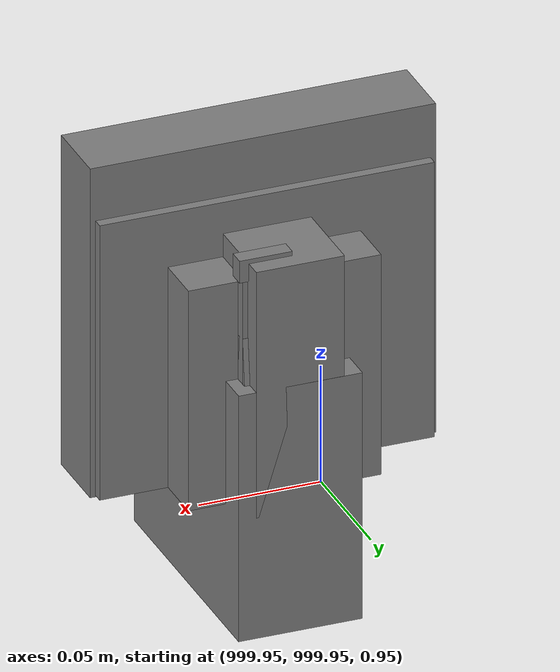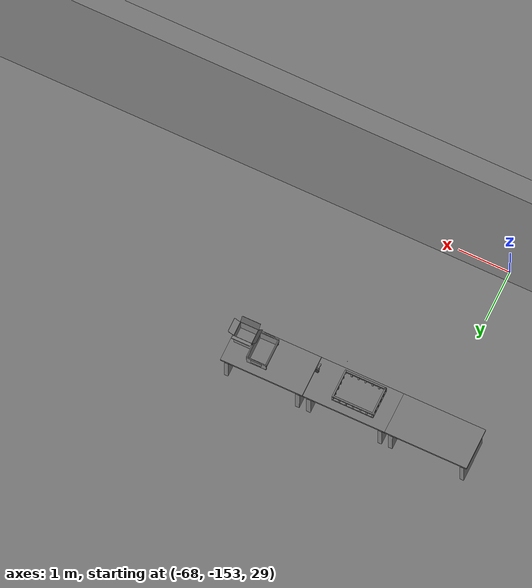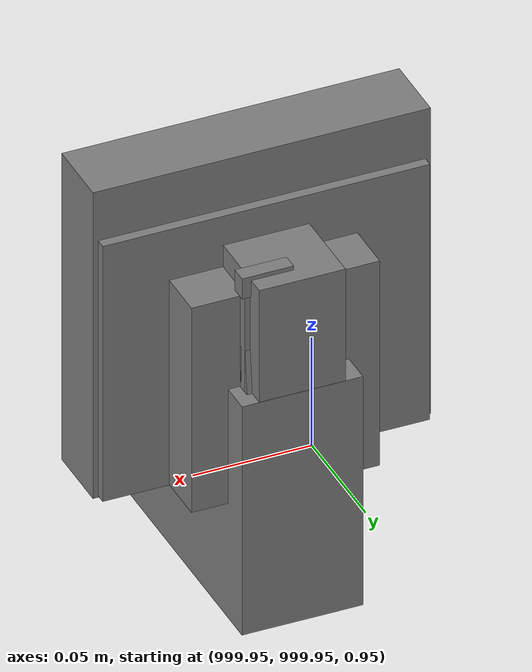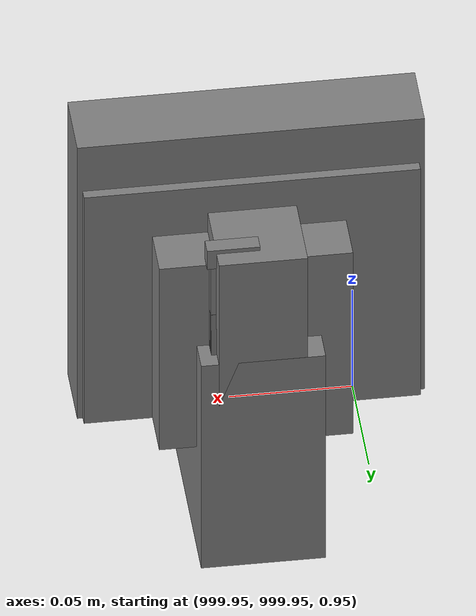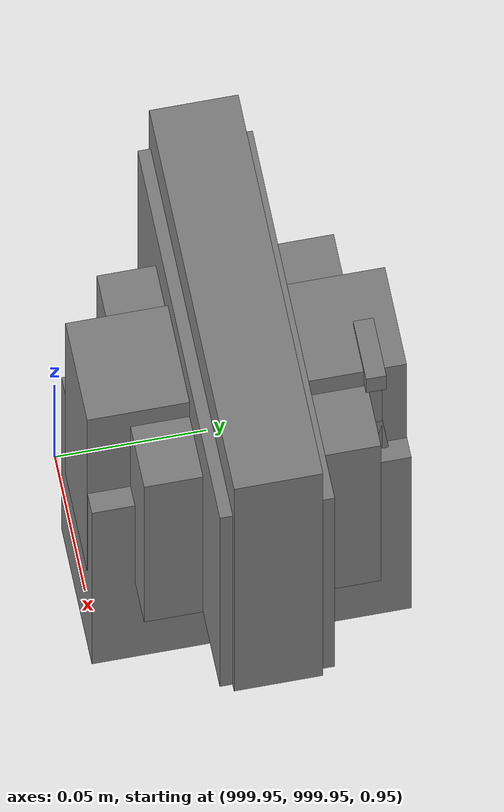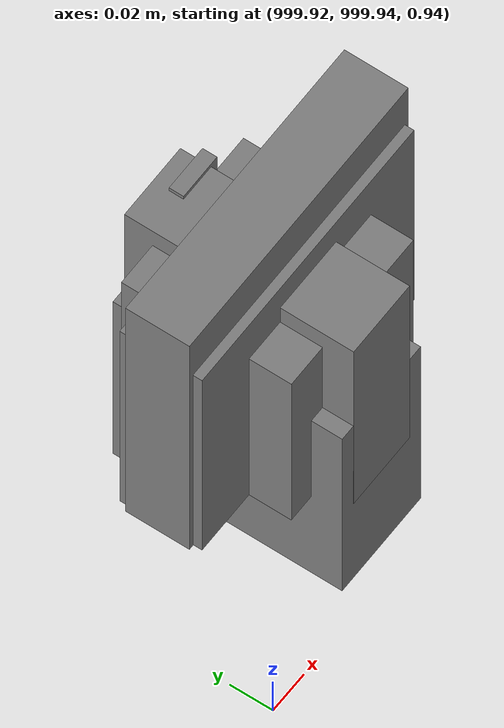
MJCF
<mujoco>
    <option gravity="0.000000000 0.000000000 -9.810000420" timestep="0.0049999999" integrator="implicitfast" density="1.225" viscosity="1.8000001e-05" noslip_iterations="10" iterations="100" sdf_iterations="50">
        <flag multiccd="disable"/>
    </option>
    <size memory="1000M"/>
    <compiler coordinate="local"/>
    <worldbody>
        <light cutoff="30" pos="0 1 1" dir="0 -1 -2"/>
        <light cutoff="30" pos="0 -1 1" dir="0 1 -2"/>
        <body pos="1000.000000000 1000.000000000 1.000000000" euler="0.000000000 0.000000000 180.000000000" name="openloong_gripper_2f85_fix_base_usda_battery_01">
            <geom contype="1" conaffinity="1" density="1000" type="box" material="" rgba="0.500000000 0.500000000 0.500000000 1.000000000" solimp="0.899999976 0.949999988 0.001000000" friction="1.000000000 0.005000000 0.000100000" solref="0.020000000 1.000000000" margin="0" condim="3" group="0" pos="-0.011123657 -0.041940309 0.101691343" quat="1.000000000 0.000000000 0.000000000 0.000000000" size="0.010800000 0.003375000 0.004725000" name="openloong_gripper_2f85_fix_base_usda_geom_666E5EC1_39F4_4B06_AA32_AE71B6772E09"/>
            <geom contype="1" conaffinity="1" density="1000" type="box" material="" rgba="0.500000000 0.500000000 0.500000000 1.000000000" solimp="0.899999976 0.949999988 0.001000000" friction="1.000000000 0.005000000 0.000100000" solref="0.020000000 1.000000000" margin="0" condim="3" group="0" pos="-0.010876465 -0.044247437 0.047066893" quat="0.998702705 -0.050920475 0.000000000 0.000000000" size="0.009450001 0.002700000 0.024975000" name="openloong_gripper_2f85_fix_base_usda_geom_437E0F07_2436_478C_BE6F_7C59D02AC53D"/>
            <geom contype="1" conaffinity="1" density="1000" type="box" material="" rgba="0.500000000 0.500000000 0.500000000 1.000000000" solimp="0.899999976 0.949999988 0.001000000" friction="1.000000000 0.005000000 0.000100000" solref="0.020000000 1.000000000" margin="0" condim="3" group="0" pos="-0.001235962 -0.000659180 0.047381196" quat="1.000000000 0.000000000 0.000000000 0.000000000" size="0.039420001 0.039150000 0.047250003" name="openloong_gripper_2f85_fix_base_usda_geom_1625E8E7_11A2_47BA_A86F_E816B4075E45"/>
            <geom contype="1" conaffinity="1" density="1000" type="box" material="" rgba="0.500000000 0.500000000 0.500000000 1.000000000" solimp="0.899999976 0.949999988 0.001000000" friction="1.000000000 0.005000000 0.000100000" solref="0.020000000 1.000000000" margin="0" condim="3" group="0" pos="-0.010876465 -0.039138794 0.009851727" quat="1.000000000 0.000000000 0.000000000 0.000000000" size="0.009450001 0.010800000 0.013500000" name="openloong_gripper_2f85_fix_base_usda_geom_5EF90FB7_3FDC_492D_B374_D60E97356B43"/>
            <geom contype="1" conaffinity="1" density="1000" type="box" material="" rgba="0.500000000 0.500000000 0.500000000 1.000000000" solimp="0.899999976 0.949999988 0.001000000" friction="1.000000000 0.005000000 0.000100000" solref="0.020000000 1.000000000" margin="0" condim="3" group="0" pos="-0.010876465 -0.041528322 0.071508206" quat="1.000000000 0.000000000 0.000000000 0.000000000" size="0.009450001 0.002700000 0.027000001" name="openloong_gripper_2f85_fix_base_usda_geom_8A3BC3E2_02F7_4774_BFC9_42B082C2ECDC"/>
            <freejoint name="openloong_gripper_2f85_fix_base_usda_battery_01_joint"/>
            <site size="0.005000000 0.005000000 0.005000000" rgba="0.500000000 0.500000000 0.500000000 1.000000000" pos="0.000000000 0.000000000 0.000000000" quat="0.999961913 0.008726500 0.000000000 0.000000000" group="0" type="sphere" name="openloong_gripper_2f85_fix_base_usda_battery_01site"/>
        </body>
        <body pos="-65.977806091 -149.336990356 31.166177750" euler="-56.007724762 -6.420886040 60.191825867" mocap="true" name="spotlight3_SpotLight"/>
        <body pos="1000.000000000 1000.000000000 1.000000000" euler="0.000000000 0.000000000 180.000000000" name="openloong_gripper_2f85_fix_base_usda_cpu_fan">
            <geom contype="1" conaffinity="1" density="1000" type="box" material="" rgba="0.500000000 0.500000000 0.500000000 1.000000000" solimp="0.899999976 0.949999988 0.001000000" friction="1.000000000 0.005000000 0.000100000" solref="0.020000000 1.000000000" margin="0" condim="3" group="0" pos="0.000000000 0.000000000 0.070034981" quat="0.000000000 0.000000000 0.000000000 1.000000000" size="0.070700005 0.014699999 0.070700005" name="openloong_gripper_2f85_fix_base_usda_geom_361C0EE5_0F7E_4848_ABDF_9C8F767372E6"/>
            <freejoint name="openloong_gripper_2f85_fix_base_usda_cpu_fan_joint"/>
            <site size="0.005000000 0.005000000 0.005000000" rgba="0.500000000 0.500000000 0.500000000 1.000000000" pos="0.000000000 0.000000000 0.000000000" quat="0.999961913 0.008726535 0.000000000 0.000000000" group="0" type="sphere" name="openloong_gripper_2f85_fix_base_usda_cpu_fancsite"/>
        </body>
        <body pos="1000.000000000 1000.000000000 1.000000000" euler="0.000000000 0.000000000 180.000000000" name="openloong_gripper_2f85_fix_base_usda_wifi_box">
            <geom contype="1" conaffinity="1" density="1000" type="box" material="" rgba="0.500000000 0.500000000 0.500000000 1.000000000" solimp="0.899999976 0.949999988 0.001000000" friction="1.000000000 0.005000000 0.000100000" solref="0.020000000 1.000000000" margin="0" condim="3" group="0" pos="0.000000000 0.000000000 0.058978677" quat="0.000000000 0.000000047 0.000000000 1.000000000" size="0.068499997 0.018999999 0.059000000" name="openloong_gripper_2f85_fix_base_usda_geom_AF85B51F_4FAF_4224_AF56_86CB27FD2FD8"/>
            <freejoint name="openloong_gripper_2f85_fix_base_usda_wifi_box_joint"/>
            <site size="0.005000000 0.005000000 0.005000000" rgba="0.500000000 0.500000000 0.500000000 1.000000000" pos="0.000000000 0.000000000 0.000000000" quat="0.999961913 0.008726500 0.000000000 0.000000000" group="0" type="sphere" name="openloong_gripper_2f85_fix_base_usda_wifi_boxsite"/>
        </body>
        <body pos="-65.958900452 -149.644012451 31.164495468" euler="3.784518480 -25.536840439 64.648818970" mocap="true" name="spotlight6_SpotLight"/>
        <body pos="1000.000000000 1000.000000000 1.000000000" euler="0.000011953 0.000005123 -179.999984741" name="openloong_gripper_2f85_fix_base_usda_intel_box">
            <geom contype="1" conaffinity="1" density="1000" type="box" material="" rgba="0.500000000 0.500000000 0.500000000 1.000000000" solimp="0.899999976 0.949999988 0.001000000" friction="1.000000000 0.005000000 0.000100000" solref="0.020000000 1.000000000" margin="0" condim="3" group="0" pos="0.000000000 -0.000067139 0.000082284" quat="0.707106709 0.000000225 0.000000253 0.707106650" size="0.052800003 0.025300000 0.052800003" name="openloong_gripper_2f85_fix_base_usda_geom_FF4CF264_64C9_47CE_A1AB_0967C17F4DF6"/>
            <freejoint name="openloong_gripper_2f85_fix_base_usda_intel_box_joint"/>
            <site size="0.005000000 0.005000000 0.005000000" rgba="0.500000000 0.500000000 0.500000000 1.000000000" pos="0.000000000 0.000000000 0.000000000" quat="0.999961913 0.008726500 0.000000000 0.000000000" group="0" type="sphere" name="openloong_gripper_2f85_fix_base_usda_intel_boxsite"/>
        </body>
        <body pos="-65.943504333 -149.367523193 31.165994644" euler="35.805015564 81.083099365 -20.970842361" mocap="true" name="spotlight5_SpotLight"/>
        <body pos="1000.000000000 999.999938965 1.000000000" euler="0.000000000 0.000000000 180.000000000" name="openloong_gripper_2f85_fix_base_usda_intelcore_i5">
            <geom contype="1" conaffinity="1" density="1000" type="box" material="" rgba="0.500000000 0.500000000 0.500000000 1.000000000" solimp="0.899999976 0.949999988 0.001000000" friction="1.000000000 0.005000000 0.000100000" solref="0.020000000 1.000000000" margin="0" condim="3" group="0" pos="0.000000000 0.000000000 0.051722717" quat="0.707106709 0.000000000 0.000000000 -0.707106769" size="0.052800000 0.018080002 0.052800000" name="openloong_gripper_2f85_fix_base_usda_geom_339D7AF7_45DA_4E77_9155_3DD3B53997B9"/>
            <freejoint name="openloong_gripper_2f85_fix_base_usda_intelcore_i5_joint"/>
            <site size="0.005000000 0.005000000 0.005000000" rgba="0.500000000 0.500000000 0.500000000 1.000000000" pos="0.000000000 0.000000000 0.000000000" quat="0.999961913 0.008726534 0.000000000 0.000000000" group="0" type="sphere" name="openloong_gripper_2f85_fix_base_usda_intelcore_i5site"/>
        </body>
        <body pos="-64.866622925 -149.383972168 30.183746338" euler="89.999984741 89.999946594 0.000000000" name="openloong_gripper_2f85_fix_base_usda_bluebox_01">
            <geom contype="1" conaffinity="1" density="1000" type="box" material="" rgba="0.500000000 0.500000000 0.500000000 1.000000000" solimp="0.899999976 0.949999988 0.001000000" friction="1.000000000 0.005000000 0.000100000" solref="0.020000000 1.000000000" margin="0" condim="3" group="0" pos="0.276580811 0.187225342 0.000068665" quat="0.707106948 0.000077471 0.707106352 0.000077486" size="0.100000001 0.057999998 0.010000000" name="openloong_gripper_2f85_fix_base_usda_geom_777C80F1_1E65_4792_97B6_EEB2B7329C1D"/>
            <geom contype="1" conaffinity="1" density="1000" type="box" material="" rgba="0.500000000 0.500000000 0.500000000 1.000000000" solimp="0.899999976 0.949999988 0.001000000" friction="1.000000000 0.005000000 0.000100000" solref="0.020000000 1.000000000" margin="0" condim="3" group="0" pos="0.000000000 0.002883911 0.000000000" quat="0.999999881 0.000000000 0.000000000 0.000000000" size="0.254000008 0.003000000 0.172000006" name="openloong_gripper_2f85_fix_base_usda_geom_A34A59CD_2777_4A6E_B283_5C9C148BE125"/>
            <geom contype="1" conaffinity="1" density="1000" type="box" material="" rgba="0.500000000 0.500000000 0.500000000 1.000000000" solimp="0.899999976 0.949999988 0.001000000" friction="1.000000000 0.005000000 0.000100000" solref="0.020000000 1.000000000" margin="0" condim="3" group="0" pos="0.000000000 0.124874115 0.173484802" quat="0.999796331 0.020176515 -0.000000015 0.000000030" size="0.259999990 0.119999997 0.007000000" name="openloong_gripper_2f85_fix_base_usda_geom_5A3D704A_889B_458D_89DA_CF9096A51058"/>
            <geom contype="1" conaffinity="1" density="1000" type="box" material="" rgba="0.500000000 0.500000000 0.500000000 1.000000000" solimp="0.899999976 0.949999988 0.001000000" friction="1.000000000 0.005000000 0.000100000" solref="0.020000000 1.000000000" margin="0" condim="3" group="0" pos="0.000000000 0.124874115 -0.173469543" quat="0.999796331 -0.020176545 -0.000000015 0.000000000" size="0.259999990 0.119999997 0.007000000" name="openloong_gripper_2f85_fix_base_usda_geom_50A4790B_327B_45C0_964C_40348B0C6DD4"/>
            <geom contype="1" conaffinity="1" density="1000" type="box" material="" rgba="0.500000000 0.500000000 0.500000000 1.000000000" solimp="0.899999976 0.949999988 0.001000000" friction="1.000000000 0.005000000 0.000100000" solref="0.020000000 1.000000000" margin="0" condim="3" group="0" pos="0.000000000 0.214008331 0.188980103" quat="0.999912977 0.013176724 0.000000015 0.000000000" size="0.259999990 0.029999999 0.012500000" name="openloong_gripper_2f85_fix_base_usda_geom_F23BF5CD_5FEE_43DF_8512_B45AE946C891"/>
            <geom contype="1" conaffinity="1" density="1000" type="box" material="" rgba="0.500000000 0.500000000 0.500000000 1.000000000" solimp="0.899999976 0.949999988 0.001000000" friction="1.000000000 0.005000000 0.000100000" solref="0.020000000 1.000000000" margin="0" condim="3" group="0" pos="-0.258361816 0.125289917 0.001876831" quat="0.702796936 -0.020792112 0.710783124 0.020769298" size="0.189999998 0.119999997 0.009000000" name="openloong_gripper_2f85_fix_base_usda_geom_FC8864F3_AFB0_4A80_B921_07D54230FD3A"/>
            <geom contype="1" conaffinity="1" density="1000" type="box" material="" rgba="0.500000000 0.500000000 0.500000000 1.000000000" solimp="0.899999976 0.949999988 0.001000000" friction="1.000000000 0.005000000 0.000100000" solref="0.020000000 1.000000000" margin="0" condim="3" group="0" pos="0.000000000 0.214008331 -0.188980103" quat="0.999912977 -0.013176769 0.000000030 0.000000015" size="0.259999990 0.029999999 0.012500000" name="openloong_gripper_2f85_fix_base_usda_geom_2588BE93_C1E6_42AA_A0B1_1D21D6099C9F"/>
            <geom contype="1" conaffinity="1" density="1000" type="box" material="" rgba="0.500000000 0.500000000 0.500000000 1.000000000" solimp="0.899999976 0.949999988 0.001000000" friction="1.000000000 0.005000000 0.000100000" solref="0.020000000 1.000000000" margin="0" condim="3" group="0" pos="-0.276611328 0.187225342 0.000068665" quat="0.707106650 0.000077441 0.707106709 0.000077456" size="0.100000001 0.057999998 0.010000000" name="openloong_gripper_2f85_fix_base_usda_geom_6A59D1E2_B739_405D_A487_D8DC36875D66"/>
            <geom contype="1" conaffinity="1" density="1000" type="box" material="" rgba="0.500000000 0.500000000 0.500000000 1.000000000" solimp="0.899999976 0.949999988 0.001000000" friction="1.000000000 0.005000000 0.000100000" solref="0.020000000 1.000000000" margin="0" condim="3" group="0" pos="0.258331299 0.125289917 0.001876831" quat="0.702851415 0.018856421 0.710823774 -0.019329369" size="0.189999998 0.119999997 0.009000000" name="openloong_gripper_2f85_fix_base_usda_geom_186BB523_62CA_4D7C_BDA4_EB96FFD1E1D9"/>
            <freejoint name="openloong_gripper_2f85_fix_base_usda_bluebox_01_joint"/>
            <site size="0.005000000 0.005000000 0.005000000" rgba="0.500000000 0.500000000 0.500000000 1.000000000" pos="0.000000000 0.000000000 0.000000000" quat="0.999961913 0.008726534 0.000000000 0.000000000" group="0" type="sphere" name="openloong_gripper_2f85_fix_base_usda_bluebox_01site"/>
        </body>
        <body pos="-64.496299744 -149.491867065 30.235729218" euler="0.000000000 0.000000000 89.999946594" name="openloong_gripper_2f85_fix_base_usda_cardboardbox_01">
            <geom contype="1" conaffinity="1" density="1000" type="box" material="" rgba="0.500000000 0.500000000 0.500000000 1.000000000" solimp="0.899999976 0.949999988 0.001000000" friction="1.000000000 0.005000000 0.000100000" solref="0.020000000 1.000000000" margin="0" condim="3" group="0" pos="-0.003166199 -0.004086494 0.005052090" quat="1.000000000 0.000000000 0.000000000 0.000000000" size="0.142499998 0.177500010 0.005000000" name="openloong_gripper_2f85_fix_base_usda_geom_3A4CFE27_864E_4BF5_9B1B_B8C0F9DDC786"/>
            <geom contype="1" conaffinity="1" density="1000" type="box" material="" rgba="0.500000000 0.500000000 0.500000000 1.000000000" solimp="0.899999976 0.949999988 0.001000000" friction="1.000000000 0.005000000 0.000100000" solref="0.020000000 1.000000000" margin="0" condim="3" group="0" pos="-0.003166199 0.170316696 0.150570869" quat="1.000000000 0.000000000 0.000000000 0.000000000" size="0.142499998 0.005000000 0.149999991" name="openloong_gripper_2f85_fix_base_usda_geom_3C1ABD02_4B07_4F9C_9D01_AD913E487047"/>
            <geom contype="1" conaffinity="1" density="1000" type="box" material="" rgba="0.500000000 0.500000000 0.500000000 1.000000000" solimp="0.899999976 0.949999988 0.001000000" friction="1.000000000 0.005000000 0.000100000" solref="0.020000000 1.000000000" margin="0" condim="3" group="0" pos="-0.147399902 -0.005307198 0.150570869" quat="1.000000000 0.000000000 0.000000000 0.000000000" size="0.005000000 0.177500010 0.149999991" name="openloong_gripper_2f85_fix_base_usda_geom_F031BE05_7F48_4433_9D06_2AFEAA089BE6"/>
            <geom contype="1" conaffinity="1" density="1000" type="box" material="" rgba="0.500000000 0.500000000 0.500000000 1.000000000" solimp="0.899999976 0.949999988 0.001000000" friction="1.000000000 0.005000000 0.000100000" solref="0.020000000 1.000000000" margin="0" condim="3" group="0" pos="0.140275955 -0.005307198 0.150570869" quat="1.000000000 0.000000000 0.000000000 0.000000000" size="0.005000000 0.177500010 0.149999991" name="openloong_gripper_2f85_fix_base_usda_geom_8F2A8826_9F19_4B98_BA79_69053996482C"/>
            <geom contype="1" conaffinity="1" density="1000" type="box" material="" rgba="0.500000000 0.500000000 0.500000000 1.000000000" solimp="0.899999976 0.949999988 0.001000000" friction="1.000000000 0.005000000 0.000100000" solref="0.020000000 1.000000000" margin="0" condim="3" group="0" pos="-0.003166199 -0.181550980 0.150570869" quat="1.000000000 0.000000000 0.000000000 0.000000000" size="0.142499998 0.005000000 0.149999991" name="openloong_gripper_2f85_fix_base_usda_geom_11CCA95F_D897_40A5_8361_6E39D70EF354"/>
            <freejoint name="openloong_gripper_2f85_fix_base_usda_cardboardbox_01_joint"/>
            <site size="0.005000000 0.005000000 0.005000000" rgba="0.500000000 0.500000000 0.500000000 1.000000000" pos="0.000000000 0.000000000 0.000000000" quat="0.999961913 0.008726535 0.000000000 0.000000000" group="0" type="sphere" name="openloong_gripper_2f85_fix_base_usda_site_F396E069_2113_4081_AD9E_4E8192FB53C5"/>
            <body pos="0.139160156 -0.004048347 0.301930904" euler="-179.999954224 49.383502960 179.999954224" name="openloong_gripper_2f85_fix_base_usda_A1_006">
                <geom contype="1" conaffinity="1" density="1000" type="box" material="" rgba="0.500000000 0.500000000 0.500000000 1.000000000" solimp="0.899999976 0.949999988 0.001000000" friction="1.000000000 0.005000000 0.000100000" solref="0.020000000 1.000000000" margin="0" condim="3" group="0" pos="-0.071587563 0.000009537 0.001745224" quat="0.999999881 0.000000000 0.000000000 0.000000000" size="0.071249999 0.179999992 0.002500000" name="openloong_gripper_2f85_fix_base_usda_geom_6D2ACC1A_1F6F_4EE3_AD29_740BC2B5ADC6"/>
                <joint armature="0" stiffness="0.07" damping="0.0099999998" axis="0.000000 1.000000 0.000000" type="hinge" name="openloong_gripper_2f85_fix_base_usda_A1_006"/>
            </body>
            <body pos="-0.145902634 -0.004086494 0.301938057" euler="-180.000000000 -60.000011444 -180.000000000" name="openloong_gripper_2f85_fix_base_usda_A2_006">
                <geom contype="1" conaffinity="1" density="1000" type="box" material="" rgba="0.500000000 0.500000000 0.500000000 1.000000000" solimp="0.899999976 0.949999988 0.001000000" friction="1.000000000 0.005000000 0.000100000" solref="0.020000000 1.000000000" margin="0" condim="3" group="0" pos="0.071268082 0.000009537 0.002717972" quat="0.000002921 0.000000000 -0.000000030 0.999999881" size="0.071249999 0.179999992 0.002500000" name="openloong_gripper_2f85_fix_base_usda_geom_5BCBF058_2E51_4068_9BE9_7AE3FD9401E4"/>
                <joint armature="0" stiffness="0.07" damping="0.0099999998" axis="0.000000 1.000000 0.000000" type="hinge" name="openloong_gripper_2f85_fix_base_usda_A2_006"/>
            </body>
            <body pos="-0.003385544 0.175991058 0.301930904" euler="-125.858116150 -0.000004561 0.000002331" name="openloong_gripper_2f85_fix_base_usda_B2_006">
                <geom contype="1" conaffinity="1" density="1000" type="box" material="" rgba="0.500000000 0.500000000 0.500000000 1.000000000" solimp="0.899999976 0.949999988 0.001000000" friction="1.000000000 0.005000000 0.000100000" solref="0.020000000 1.000000000" margin="0" condim="3" group="0" pos="0.000009537 -0.070939064 -0.002470016" quat="0.999614120 0.027776197 -0.000000015 0.000000030" size="0.137500003 0.064999998 0.005000000" name="openloong_gripper_2f85_fix_base_usda_geom_73D4CDC4_CE32_4024_956C_9399FC7C8E0C"/>
                <joint armature="0" stiffness="0.07" damping="0.0099999998" axis="1.000000 0.000000 0.000000" type="hinge" name="openloong_gripper_2f85_fix_base_usda_B2_006"/>
            </body>
            <body pos="-0.003385544 -0.184140205 0.301938057" euler="147.805557251 0.000000000 0.000000000" name="openloong_gripper_2f85_fix_base_usda_B1_006">
                <geom contype="1" conaffinity="1" density="1000" type="box" material="" rgba="0.500000000 0.500000000 0.500000000 1.000000000" solimp="0.899999976 0.949999988 0.001000000" friction="1.000000000 0.005000000 0.000100000" solref="0.020000000 1.000000000" margin="0" condim="3" group="0" pos="-0.000028610 0.070202351 -0.002703667" quat="0.999614179 -0.027776167 0.000000000 0.000000000" size="0.137500003 0.064999998 0.005000000" name="openloong_gripper_2f85_fix_base_usda_geom_996E018B_7AE0_4E10_97D8_6AF0E42CA54A"/>
                <joint armature="0" stiffness="0.07" damping="0.0099999998" axis="1.000000 0.000000 0.000000" type="hinge" name="openloong_gripper_2f85_fix_base_usda_B1_006"/>
            </body>
        </body>
        <body pos="-65.882858276 -149.481979370 30.229999542" euler="-64.487716675 0.000000000 0.000000000" name="openloong_gripper_2f85_fix_base_usda_Barcode">
            <geom contype="1" conaffinity="1" density="1000" type="box" material="" rgba="0.500000000 0.500000000 0.500000000 1.000000000" solimp="0.899999976 0.949999988 0.001000000" friction="1.000000000 0.005000000 0.000100000" solref="0.020000000 1.000000000" margin="0" condim="3" group="0" pos="0.000000000 0.013038635 0.001419067" quat="0.000000000 0.000000000 0.000000000 1.000000119" size="0.034000002 0.010000000 0.017999999" name="openloong_gripper_2f85_fix_base_usda_geom_2739C319_726D_4534_9339_9B0DD38C84F9"/>
            <geom contype="1" conaffinity="1" density="1000" type="box" material="" rgba="0.500000000 0.500000000 0.500000000 1.000000000" solimp="0.899999976 0.949999988 0.001000000" friction="1.000000000 0.005000000 0.000100000" solref="0.020000000 1.000000000" margin="0" condim="3" group="0" pos="0.000000000 -0.035301208 -0.007095337" quat="0.000000000 0.000000000 -0.043619365 0.999048233" size="0.028999999 0.010000000 0.020000000" name="openloong_gripper_2f85_fix_base_usda_geom_8FBEABC5_0B3B_4DB9_B31C_4062881387DB"/>
            <geom contype="1" conaffinity="1" density="1000" type="box" material="" rgba="0.500000000 0.500000000 0.500000000 1.000000000" solimp="0.899999976 0.949999988 0.001000000" friction="1.000000000 0.005000000 0.000100000" solref="0.020000000 1.000000000" margin="0" condim="3" group="0" pos="0.000000000 -0.043411255 -0.011749268" quat="0.922262907 0.386563420 0.000000000 0.000000000" size="0.026000001 0.010000000 0.020000000" name="openloong_gripper_2f85_fix_base_usda_geom_61202B94_AD96_47BE_82CE_9696335EECB8"/>
            <geom contype="1" conaffinity="1" density="1000" type="box" material="" rgba="0.500000000 0.500000000 0.500000000 1.000000000" solimp="0.899999976 0.949999988 0.001000000" friction="1.000000000 0.005000000 0.000100000" solref="0.020000000 1.000000000" margin="0" condim="3" group="0" pos="0.000000000 -0.016967773 -0.031860352" quat="0.000000000 0.000000000 0.000000000 1.000000119" size="0.008000000 0.010000000 0.013000000" name="openloong_gripper_2f85_fix_base_usda_geom_4A2FEC0C_DC4C_420B_9ED7_037939144DD8"/>
            <geom contype="1" conaffinity="1" density="1000" type="box" material="" rgba="0.500000000 0.500000000 0.500000000 1.000000000" solimp="0.899999976 0.949999988 0.001000000" friction="1.000000000 0.005000000 0.000100000" solref="0.020000000 1.000000000" margin="0" condim="3" group="0" pos="0.000000000 -0.001869202 0.000312805" quat="0.953716993 0.300705761 0.000000000 0.000000000" size="0.032000002 0.010000000 0.018999999" name="openloong_gripper_2f85_fix_base_usda_geom_81132B7B_E9A2_44BE_AA2A_74F8DC21FC24"/>
            <geom contype="1" conaffinity="1" density="1000" type="box" material="" rgba="0.500000000 0.500000000 0.500000000 1.000000000" solimp="0.899999976 0.949999988 0.001000000" friction="1.000000000 0.005000000 0.000100000" solref="0.020000000 1.000000000" margin="0" condim="3" group="0" pos="0.000000000 -0.019531250 -0.003173828" quat="0.953716993 0.300705761 0.000000000 0.000000000" size="0.030999999 0.010000000 0.020000000" name="openloong_gripper_2f85_fix_base_usda_geom_EAA9F7A5_A692_43F4_B9B2_69892B14CD3F"/>
            <geom contype="1" conaffinity="1" density="1000" type="box" material="" rgba="0.500000000 0.500000000 0.500000000 1.000000000" solimp="0.899999976 0.949999988 0.001000000" friction="1.000000000 0.005000000 0.000100000" solref="0.020000000 1.000000000" margin="0" condim="3" group="0" pos="0.000000000 -0.035301208 -0.007095337" quat="0.953716993 0.300705761 0.000000000 0.000000000" size="0.028999999 0.010000000 0.020000000" name="openloong_gripper_2f85_fix_base_usda_geom_61D9E8B9_214F_42CC_A1C1_5146F53CB020"/>
            <geom contype="1" conaffinity="1" density="1000" type="box" material="" rgba="0.500000000 0.500000000 0.500000000 1.000000000" solimp="0.899999976 0.949999988 0.001000000" friction="1.000000000 0.005000000 0.000100000" solref="0.020000000 1.000000000" margin="0" condim="3" group="0" pos="0.000000000 -0.042617798 -0.071121216" quat="0.000000000 0.000000000 0.000000000 1.000000119" size="0.013000000 0.021000000 0.059999999" name="openloong_gripper_2f85_fix_base_usda_geom_E1977A48_3B7F_49D2_8074_131054D48693"/>
            <freejoint name="openloong_gripper_2f85_fix_base_usda_Barcode_joint"/>
            <site size="0.005000000 0.005000000 0.005000000" rgba="0.500000000 0.500000000 0.500000000 1.000000000" pos="0.000000000 0.000000000 0.000000000" quat="1.000000000 0.000000000 0.000000000 0.000000000" group="0" type="sphere" name="openloong_gripper_2f85_fix_base_usda_Barcode_site"/>
        </body>
        <body pos="-66.745018005 -149.392349243 30.184000015" euler="0.000000000 0.000000000 89.999946594" name="[22332348144135]_Basket_01">
            <geom contype="1" conaffinity="1" density="1000" type="box" material="" rgba="0.500000000 0.500000000 0.500000000 1.000000000" solimp="0.899999976 0.949999988 0.001000000" friction="1.000000000 0.005000000 0.000100000" solref="0.020000000 1.000000000" margin="0" condim="3" group="0" pos="-0.052425385 0.389207840 0.089787483" quat="0.707107008 0.000000000 0.000000000 0.707106411" size="0.014249999 0.014249999 0.059999999" name="[22332348144135]_geom_31D691D8_5247_4CA7_A441_9F2831A12362"/>
            <geom contype="1" conaffinity="1" density="1000" type="box" material="" rgba="0.500000000 0.500000000 0.500000000 1.000000000" solimp="0.899999976 0.949999988 0.001000000" friction="1.000000000 0.005000000 0.000100000" solref="0.020000000 1.000000000" margin="0" condim="3" group="0" pos="0.264015198 -0.133043289 0.089787483" quat="0.707107008 0.000000000 0.000000000 0.707106411" size="0.014249999 0.014249999 0.059999999" name="[22332348144135]_geom_12304540_5A9E_4891_964E_63F110C492A3"/>
            <geom contype="1" conaffinity="1" density="1000" type="box" material="" rgba="0.500000000 0.500000000 0.500000000 1.000000000" solimp="0.899999976 0.949999988 0.001000000" friction="1.000000000 0.005000000 0.000100000" solref="0.020000000 1.000000000" margin="0" condim="3" group="0" pos="-0.264015198 -0.265548706 0.089793205" quat="0.707107008 0.000000000 0.000000000 0.707106411" size="0.014249999 0.014249999 0.059999999" name="[22332348144135]_geom_B49C4BAE_D0E3_493F_90CE_D067010E7DA2"/>
            <geom contype="1" conaffinity="1" density="1000" type="box" material="" rgba="0.500000000 0.500000000 0.500000000 1.000000000" solimp="0.899999976 0.949999988 0.001000000" friction="1.000000000 0.005000000 0.000100000" solref="0.020000000 1.000000000" margin="0" condim="3" group="0" pos="-0.160263062 -0.389322281 0.089793205" quat="0.707107008 0.000000000 0.000000000 0.707106411" size="0.014249999 0.014249999 0.059999999" name="[22332348144135]_geom_0356B010_0DE7_43A6_9231_5F62A2DE5713"/>
            <geom contype="1" conaffinity="1" density="1000" type="box" material="" rgba="0.500000000 0.500000000 0.500000000 1.000000000" solimp="0.899999976 0.949999988 0.001000000" friction="1.000000000 0.005000000 0.000100000" solref="0.020000000 1.000000000" margin="0" condim="3" group="0" pos="0.162265778 -0.389322281 0.089787483" quat="0.707107008 0.000000000 0.000000000 0.707106411" size="0.014249999 0.014249999 0.059999999" name="[22332348144135]_geom_6549739F_F5BC_4AAC_8B1C_B40D839F7916"/>
            <geom contype="1" conaffinity="1" density="1000" type="box" material="" rgba="0.500000000 0.500000000 0.500000000 1.000000000" solimp="0.899999976 0.949999988 0.001000000" friction="1.000000000 0.005000000 0.000100000" solref="0.020000000 1.000000000" margin="0" condim="3" group="0" pos="0.264015198 0.389207840 0.089787483" quat="0.707107008 0.000000000 0.000000000 0.707106411" size="0.014249999 0.014249999 0.059999999" name="[22332348144135]_geom_2E9187DC_1DAB_4274_A97C_0726245A7B49"/>
            <geom contype="1" conaffinity="1" density="1000" type="box" material="" rgba="0.500000000 0.500000000 0.500000000 1.000000000" solimp="0.899999976 0.949999988 0.001000000" friction="1.000000000 0.005000000 0.000100000" solref="0.020000000 1.000000000" margin="0" condim="3" group="0" pos="-0.264015198 -0.133043289 0.089793205" quat="0.707107008 0.000000000 0.000000000 0.707106411" size="0.014249999 0.014249999 0.059999999" name="[22332348144135]_geom_7F3C86ED_D91B_4AEE_BA52_D8EF0E61D259"/>
            <geom contype="1" conaffinity="1" density="1000" type="box" material="" rgba="0.500000000 0.500000000 0.500000000 1.000000000" solimp="0.899999976 0.949999988 0.001000000" friction="1.000000000 0.005000000 0.000100000" solref="0.020000000 1.000000000" margin="0" condim="3" group="0" pos="-0.264026642 0.269256592 0.089793205" quat="0.707107008 0.000000000 0.000000000 0.707106411" size="0.014249999 0.014249999 0.059999999" name="[22332348144135]_geom_C274984D_8F77_413A_B067_5CE626AABFEA"/>
            <geom contype="1" conaffinity="1" density="1000" type="box" material="" rgba="0.500000000 0.500000000 0.500000000 1.000000000" solimp="0.899999976 0.949999988 0.001000000" friction="1.000000000 0.005000000 0.000100000" solref="0.020000000 1.000000000" margin="0" condim="3" group="0" pos="0.054462433 0.389207840 0.089787483" quat="0.707107008 0.000000000 0.000000000 0.707106411" size="0.014249999 0.014249999 0.059999999" name="[22332348144135]_geom_0BDEE064_4146_413A_A768_6E708195B885"/>
            <geom contype="1" conaffinity="1" density="1000" type="box" material="" rgba="0.500000000 0.500000000 0.500000000 1.000000000" solimp="0.899999976 0.949999988 0.001000000" friction="1.000000000 0.005000000 0.000100000" solref="0.020000000 1.000000000" margin="0" condim="3" group="0" pos="0.054462433 -0.389322281 0.089787483" quat="0.707107008 0.000000000 0.000000000 0.707106411" size="0.014249999 0.014249999 0.059999999" name="[22332348144135]_geom_87D76B44_2763_4E2F_8595_3C12F0EE731F"/>
            <geom contype="1" conaffinity="1" density="1000" type="box" material="" rgba="0.500000000 0.500000000 0.500000000 1.000000000" solimp="0.899999976 0.949999988 0.001000000" friction="1.000000000 0.005000000 0.000100000" solref="0.020000000 1.000000000" margin="0" condim="3" group="0" pos="0.264015198 0.269256592 0.089793205" quat="0.707107008 0.000000000 0.000000000 0.707106411" size="0.014249999 0.014249999 0.059999999" name="[22332348144135]_geom_D15D31D2_E6A3_4489_9B58_BF5451C80D1B"/>
            <geom contype="1" conaffinity="1" density="1000" type="box" material="" rgba="0.500000000 0.500000000 0.500000000 1.000000000" solimp="0.899999976 0.949999988 0.001000000" friction="1.000000000 0.005000000 0.000100000" solref="0.020000000 1.000000000" margin="0" condim="3" group="0" pos="0.264015198 -0.389322281 0.089787483" quat="0.707107008 0.000000000 0.000000000 0.707106411" size="0.014249999 0.014249999 0.059999999" name="[22332348144135]_geom_E0C905EA_AB91_4EFC_8939_ED7C413EEDF1"/>
            <geom contype="1" conaffinity="1" density="1000" type="box" material="" rgba="0.500000000 0.500000000 0.500000000 1.000000000" solimp="0.899999976 0.949999988 0.001000000" friction="1.000000000 0.005000000 0.000100000" solref="0.020000000 1.000000000" margin="0" condim="3" group="0" pos="0.000000000 0.000000000 0.015998840" quat="0.707107008 0.000000000 0.000000000 0.707106411" size="0.403499991 0.279000014 0.015750000" name="[22332348144135]_geom_46FD27FD_20DB_408C_B095_76F372EA3AF9"/>
            <geom contype="1" conaffinity="1" density="1000" type="box" material="" rgba="0.500000000 0.500000000 0.500000000 1.000000000" solimp="0.899999976 0.949999988 0.001000000" friction="1.000000000 0.005000000 0.000100000" solref="0.020000000 1.000000000" margin="0" condim="3" group="0" pos="0.000000000 -0.389476776 0.163619041" quat="0.707107008 0.000000000 0.000000000 0.707106411" size="0.015000000 0.277500004 0.015750000" name="[22332348144135]_geom_4DE2ED37_7523_4B3D_B394_1D9B8A295E29"/>
            <geom contype="1" conaffinity="1" density="1000" type="box" material="" rgba="0.500000000 0.500000000 0.500000000 1.000000000" solimp="0.899999976 0.949999988 0.001000000" friction="1.000000000 0.005000000 0.000100000" solref="0.020000000 1.000000000" margin="0" condim="3" group="0" pos="0.162265778 0.389207840 0.089787483" quat="0.707107008 0.000000000 0.000000000 0.707106411" size="0.014249999 0.014249999 0.059999999" name="[22332348144135]_geom_4B95FFF2_36FC_4E7E_A7B1_98F84B61DD23"/>
            <geom contype="1" conaffinity="1" density="1000" type="box" material="" rgba="0.500000000 0.500000000 0.500000000 1.000000000" solimp="0.899999976 0.949999988 0.001000000" friction="1.000000000 0.005000000 0.000100000" solref="0.020000000 1.000000000" margin="0" condim="3" group="0" pos="0.000000000 0.389471054 0.163619041" quat="0.707107008 0.000000000 0.000000000 0.707106411" size="0.015000000 0.277500004 0.015750000" name="[22332348144135]_geom_A1452680_39CA_4EF2_B8CB_6123B7E23685"/>
            <geom contype="1" conaffinity="1" density="1000" type="box" material="" rgba="0.500000000 0.500000000 0.500000000 1.000000000" solimp="0.899999976 0.949999988 0.001000000" friction="1.000000000 0.005000000 0.000100000" solref="0.020000000 1.000000000" margin="0" condim="3" group="0" pos="-0.263511658 0.000000000 0.163619041" quat="0.707107008 0.000000000 0.000000000 0.707106411" size="0.403499991 0.015000000 0.015750000" name="[22332348144135]_geom_32AA7897_FA50_4595_BD64_D65136C3ED6C"/>
            <geom contype="1" conaffinity="1" density="1000" type="box" material="" rgba="0.500000000 0.500000000 0.500000000 1.000000000" solimp="0.899999976 0.949999988 0.001000000" friction="1.000000000 0.005000000 0.000100000" solref="0.020000000 1.000000000" margin="0" condim="3" group="0" pos="-0.264015198 0.141334534 0.089793205" quat="0.707107008 0.000000000 0.000000000 0.707106411" size="0.014249999 0.014249999 0.059999999" name="[22332348144135]_geom_6DC5AFD8_C958_4D17_A37B_CC1881E5B3B1"/>
            <geom contype="1" conaffinity="1" density="1000" type="box" material="" rgba="0.500000000 0.500000000 0.500000000 1.000000000" solimp="0.899999976 0.949999988 0.001000000" friction="1.000000000 0.005000000 0.000100000" solref="0.020000000 1.000000000" margin="0" condim="3" group="0" pos="0.264015198 -0.265548706 0.089787483" quat="0.707107008 0.000000000 0.000000000 0.707106411" size="0.014249999 0.014249999 0.059999999" name="[22332348144135]_geom_D24A269A_D7C5_43D1_AB65_496428ABE8C9"/>
            <geom contype="1" conaffinity="1" density="1000" type="box" material="" rgba="0.500000000 0.500000000 0.500000000 1.000000000" solimp="0.899999976 0.949999988 0.001000000" friction="1.000000000 0.005000000 0.000100000" solref="0.020000000 1.000000000" margin="0" condim="3" group="0" pos="-0.160263062 0.389207840 0.089787483" quat="0.707107008 0.000000000 0.000000000 0.707106411" size="0.014249999 0.014249999 0.059999999" name="[22332348144135]_geom_57499ED8_1B46_44BC_AF07_FA1A2DE5C635"/>
            <geom contype="1" conaffinity="1" density="1000" type="box" material="" rgba="0.500000000 0.500000000 0.500000000 1.000000000" solimp="0.899999976 0.949999988 0.001000000" friction="1.000000000 0.005000000 0.000100000" solref="0.020000000 1.000000000" margin="0" condim="3" group="0" pos="-0.052425385 -0.389322281 0.089787483" quat="0.707107008 0.000000000 0.000000000 0.707106411" size="0.014249999 0.014249999 0.059999999" name="[22332348144135]_geom_4FD0D0DC_02E4_425B_88C9_471B325618FE"/>
            <geom contype="1" conaffinity="1" density="1000" type="box" material="" rgba="0.500000000 0.500000000 0.500000000 1.000000000" solimp="0.899999976 0.949999988 0.001000000" friction="1.000000000 0.005000000 0.000100000" solref="0.020000000 1.000000000" margin="0" condim="3" group="0" pos="-0.264026642 -0.389322281 0.089793205" quat="0.707107008 0.000000000 0.000000000 0.707106411" size="0.014249999 0.014249999 0.059999999" name="[22332348144135]_geom_AF223E4A_8689_4712_A0CE_5D83133BAE69"/>
            <geom contype="1" conaffinity="1" density="1000" type="box" material="" rgba="0.500000000 0.500000000 0.500000000 1.000000000" solimp="0.899999976 0.949999988 0.001000000" friction="1.000000000 0.005000000 0.000100000" solref="0.020000000 1.000000000" margin="0" condim="3" group="0" pos="0.264015198 0.141334534 0.089787483" quat="0.707107008 0.000000000 0.000000000 0.707106411" size="0.014249999 0.014249999 0.059999999" name="[22332348144135]_geom_A131092E_21DB_481F_B712_500772D96A54"/>
            <geom contype="1" conaffinity="1" density="1000" type="box" material="" rgba="0.500000000 0.500000000 0.500000000 1.000000000" solimp="0.899999976 0.949999988 0.001000000" friction="1.000000000 0.005000000 0.000100000" solref="0.020000000 1.000000000" margin="0" condim="3" group="0" pos="-0.264015198 0.389207840 0.089793205" quat="0.707107008 0.000000000 0.000000000 0.707106411" size="0.014249999 0.014249999 0.059999999" name="[22332348144135]_geom_D65E0B89_F251_4528_9B9F_865F7664B79E"/>
            <geom contype="1" conaffinity="1" density="1000" type="box" material="" rgba="0.500000000 0.500000000 0.500000000 1.000000000" solimp="0.899999976 0.949999988 0.001000000" friction="1.000000000 0.005000000 0.000100000" solref="0.020000000 1.000000000" margin="0" condim="3" group="0" pos="0.264015198 0.004480362 0.089787483" quat="0.707107008 0.000000000 0.000000000 0.707106411" size="0.014249999 0.014249999 0.059999999" name="[22332348144135]_geom_C7C4F016_139E_4837_9836_894ADF8E9F59"/>
            <geom contype="1" conaffinity="1" density="1000" type="box" material="" rgba="0.500000000 0.500000000 0.500000000 1.000000000" solimp="0.899999976 0.949999988 0.001000000" friction="1.000000000 0.005000000 0.000100000" solref="0.020000000 1.000000000" margin="0" condim="3" group="0" pos="0.263694763 -0.000011444 0.163619041" quat="0.707107008 0.000000000 0.000000000 0.707106411" size="0.403499991 0.015000000 0.015750000" name="[22332348144135]_geom_09D6A284_F0FB_4B05_9462_61260FEBE73D"/>
            <geom contype="1" conaffinity="1" density="1000" type="box" material="" rgba="0.500000000 0.500000000 0.500000000 1.000000000" solimp="0.899999976 0.949999988 0.001000000" friction="1.000000000 0.005000000 0.000100000" solref="0.020000000 1.000000000" margin="0" condim="3" group="0" pos="-0.264015198 0.004480362 0.089793205" quat="0.707107008 0.000000000 0.000000000 0.707106411" size="0.014249999 0.014249999 0.059999999" name="[22332348144135]_geom_1BA1FFD8_21FD_4C0C_9C44_BE429CC268C0"/>
            <freejoint name="[22332348144135]_joint_B68A5F0A_D95F_4541_8035_E11712460441"/>
        </body>
        <body pos="0.000000000 0.000000000 0.000000000" euler="0.000000000 0.000000000 0.000000000" name="Static Objects_Static Objects">
            <geom contype="1" conaffinity="1" density="1000" type="box" material="" rgba="0.500000000 0.500000000 0.500000000 1.000000000" solimp="0.899999976 0.949999988 0.001000000" friction="1.000000000 0.005000000 0.000100000" solref="0.020000000 1.000000000" margin="0" condim="3" group="0" pos="-67.544113159 -149.365814209 29.727830887" quat="0.500000417 0.499999970 0.499999553 0.499999970" size="0.381000012 0.319999993 0.041000001" name="Static Objects_geom_24D3A61A_A28E_4507_8780_5F6AE39745EC"/>
            <geom contype="1" conaffinity="1" density="1000" type="box" material="" rgba="0.500000000 0.500000000 0.500000000 1.000000000" solimp="0.899999976 0.949999988 0.001000000" friction="1.000000000 0.005000000 0.000100000" solref="0.020000000 1.000000000" margin="0" condim="3" group="0" pos="-68.239501953 -149.365814209 30.086868286" quat="0.500000417 0.499999970 0.499999553 0.499999970" size="0.370999992 0.039500002 0.745000005" name="Static Objects_geom_13CDA60D_5D7B_4CB3_BDB3_6112F969F2BF"/>
            <geom contype="1" conaffinity="1" density="1000" type="box" material="" rgba="0.500000000 0.500000000 0.500000000 1.000000000" solimp="0.899999976 0.949999988 0.001000000" friction="1.000000000 0.005000000 0.000100000" solref="0.020000000 1.000000000" margin="0" condim="3" group="0" pos="-68.239501953 -149.365814209 30.147235870" quat="0.500000417 0.499999970 0.499999553 0.499999970" size="0.400000006 0.022000000 0.800000012" name="Static Objects_geom_2E7E7C5D_FDE2_4005_88A4_7473E0C84875"/>
            <geom contype="1" conaffinity="1" density="1000" type="box" material="" rgba="0.500000000 0.500000000 0.500000000 1.000000000" solimp="0.899999976 0.949999988 0.001000000" friction="1.000000000 0.005000000 0.000100000" solref="0.020000000 1.000000000" margin="0" condim="3" group="0" pos="-68.934890747 -149.365814209 29.727830887" quat="0.500000417 0.499999970 0.499999553 0.499999970" size="0.381000012 0.319999993 0.041000001" name="Static Objects_geom_03CE0F1C_F082_4E81_8539_87E559850532"/>
            <geom contype="1" conaffinity="1" density="1000" type="box" material="" rgba="0.500000000 0.500000000 0.500000000 1.000000000" solimp="0.899999976 0.949999988 0.001000000" friction="1.000000000 0.005000000 0.000100000" solref="0.020000000 1.000000000" margin="0" condim="3" group="0" pos="-68.239501953 -149.365814209 29.561563492" quat="0.500000417 0.499999970 0.499999553 0.499999970" size="0.020000000 0.022000000 0.660000026" name="Static Objects_geom_F9B7476B_8898_430F_BC9E_63018636898E"/>
            <geom contype="1" conaffinity="1" density="1000" type="box" material="" rgba="0.500000000 0.500000000 0.500000000 1.000000000" solimp="0.899999976 0.949999988 0.001000000" friction="1.000000000 0.005000000 0.000100000" solref="0.020000000 1.000000000" margin="0" condim="3" group="0" pos="-65.945671082 -149.365814209 29.727830887" quat="0.500000417 0.499999970 0.499999553 0.499999970" size="0.381000012 0.319999993 0.041000001" name="Static Objects_geom_C92DA32F_86DF_4AD6_8D64_F80CA48265E8"/>
            <geom contype="1" conaffinity="1" density="1000" type="box" material="" rgba="0.500000000 0.500000000 0.500000000 1.000000000" solimp="0.899999976 0.949999988 0.001000000" friction="1.000000000 0.005000000 0.000100000" solref="0.020000000 1.000000000" margin="0" condim="3" group="0" pos="-66.641059875 -149.365814209 30.086868286" quat="0.500000417 0.499999970 0.499999553 0.499999970" size="0.370999992 0.039500002 0.745000005" name="Static Objects_geom_6A7C7989_598F_47EC_A757_9ABAEBCAC0A6"/>
            <geom contype="1" conaffinity="1" density="1000" type="box" material="" rgba="0.500000000 0.500000000 0.500000000 1.000000000" solimp="0.899999976 0.949999988 0.001000000" friction="1.000000000 0.005000000 0.000100000" solref="0.020000000 1.000000000" margin="0" condim="3" group="0" pos="-66.641059875 -149.365814209 30.147235870" quat="0.500000417 0.499999970 0.499999553 0.499999970" size="0.400000006 0.022000000 0.800000012" name="Static Objects_geom_D0814AB4_B577_4761_9D8A_88DB7D17F156"/>
            <geom contype="1" conaffinity="1" density="1000" type="box" material="" rgba="0.500000000 0.500000000 0.500000000 1.000000000" solimp="0.899999976 0.949999988 0.001000000" friction="1.000000000 0.005000000 0.000100000" solref="0.020000000 1.000000000" margin="0" condim="3" group="0" pos="-67.336448669 -149.365814209 29.727830887" quat="0.500000417 0.499999970 0.499999553 0.499999970" size="0.381000012 0.319999993 0.041000001" name="Static Objects_geom_984F82F6_8B23_4C64_B906_C9636DD8A1DD"/>
            <geom contype="1" conaffinity="1" density="1000" type="box" material="" rgba="0.500000000 0.500000000 0.500000000 1.000000000" solimp="0.899999976 0.949999988 0.001000000" friction="1.000000000 0.005000000 0.000100000" solref="0.020000000 1.000000000" margin="0" condim="3" group="0" pos="-66.641059875 -149.365814209 29.561563492" quat="0.500000417 0.499999970 0.499999553 0.499999970" size="0.020000000 0.022000000 0.660000026" name="Static Objects_geom_EB610E16_ABCB_46E7_B717_22100F549684"/>
            <geom contype="1" conaffinity="1" density="1000" type="box" material="" rgba="0.500000000 0.500000000 0.500000000 1.000000000" solimp="0.899999976 0.949999988 0.001000000" friction="1.000000000 0.005000000 0.000100000" solref="0.020000000 1.000000000" margin="0" condim="3" group="0" pos="-64.338577271 -149.365814209 29.727830887" quat="0.500000417 0.499999970 0.499999553 0.499999970" size="0.381000012 0.319999993 0.041000001" name="Static Objects_geom_28B193E1_18F7_4DC2_A7A7_19C023D8BFEE"/>
            <geom contype="1" conaffinity="1" density="1000" type="box" material="" rgba="0.500000000 0.500000000 0.500000000 1.000000000" solimp="0.899999976 0.949999988 0.001000000" friction="1.000000000 0.005000000 0.000100000" solref="0.020000000 1.000000000" margin="0" condim="3" group="0" pos="-65.033966064 -149.365814209 30.086868286" quat="0.500000417 0.499999970 0.499999553 0.499999970" size="0.370999992 0.039500002 0.745000005" name="Static Objects_geom_16B21BAB_61D9_4916_B4DA_9204B7818955"/>
            <geom contype="1" conaffinity="1" density="1000" type="box" material="" rgba="0.500000000 0.500000000 0.500000000 1.000000000" solimp="0.899999976 0.949999988 0.001000000" friction="1.000000000 0.005000000 0.000100000" solref="0.020000000 1.000000000" margin="0" condim="3" group="0" pos="-65.033966064 -149.365814209 30.147235870" quat="0.500000417 0.499999970 0.499999553 0.499999970" size="0.400000006 0.022000000 0.800000012" name="Static Objects_geom_E28CDDFD_0088_4753_B5AE_5AD2A7476604"/>
            <geom contype="1" conaffinity="1" density="1000" type="box" material="" rgba="0.500000000 0.500000000 0.500000000 1.000000000" solimp="0.899999976 0.949999988 0.001000000" friction="1.000000000 0.005000000 0.000100000" solref="0.020000000 1.000000000" margin="0" condim="3" group="0" pos="-65.729354858 -149.365814209 29.727830887" quat="0.500000417 0.499999970 0.499999553 0.499999970" size="0.381000012 0.319999993 0.041000001" name="Static Objects_geom_3591C8A2_4A81_4543_946A_08C14A6E6BB2"/>
            <geom contype="1" conaffinity="1" density="1000" type="box" material="" rgba="0.500000000 0.500000000 0.500000000 1.000000000" solimp="0.899999976 0.949999988 0.001000000" friction="1.000000000 0.005000000 0.000100000" solref="0.020000000 1.000000000" margin="0" condim="3" group="0" pos="-65.033966064 -149.365814209 29.561563492" quat="0.500000417 0.499999970 0.499999553 0.499999970" size="0.020000000 0.022000000 0.660000026" name="Static Objects_geom_7DEDEEC3_9ED5_4B43_B21D_AFB2D25FCB98"/>
            <geom contype="1" conaffinity="1" density="1000" type="box" material="" rgba="0.500000000 0.500000000 0.500000000 1.000000000" solimp="0.899999976 0.949999988 0.001000000" friction="1.000000000 0.005000000 0.000100000" solref="0.020000000 1.000000000" margin="0" condim="3" group="0" pos="-61.754566193 -137.853729248 33.906845093" quat="0.707107067 0.000000000 0.000000000 0.707106471" size="0.759999990 0.759999990 4.500000000" name="Static Objects_geom_B36883C7_6777_4CC4_B617_104560D2A18F"/>
            <geom contype="1" conaffinity="1" density="1000" type="box" material="" rgba="0.500000000 0.500000000 0.500000000 1.000000000" solimp="0.899999976 0.949999988 0.001000000" friction="1.000000000 0.005000000 0.000100000" solref="0.020000000 1.000000000" margin="0" condim="3" group="0" pos="-57.511135101 -144.927108765 31.707921982" quat="1.000000000 0.000000000 0.000000000 0.000000000" size="0.200000003 8.000000000 2.299999952" name="Static Objects_geom_4AD9117F_D377_4F98_A434_B1D38D7B5382"/>
            <geom contype="1" conaffinity="1" density="1000" type="box" material="" rgba="0.500000000 0.500000000 0.500000000 1.000000000" solimp="0.899999976 0.949999988 0.001000000" friction="1.000000000 0.005000000 0.000100000" solref="0.020000000 1.000000000" margin="0" condim="3" group="0" pos="-80.517646790 -157.574050903 31.688196182" quat="0.707107067 0.000000000 0.000000000 0.707106471" size="0.600000024 0.600000024 2.299999952" name="Static Objects_geom_DDF2DFC3_341E_48EA_BE30_07F49BECCFA6"/>
            <geom contype="1" conaffinity="1" density="1000" type="box" material="" rgba="0.500000000 0.500000000 0.500000000 1.000000000" solimp="0.899999976 0.949999988 0.001000000" friction="1.000000000 0.005000000 0.000100000" solref="0.020000000 1.000000000" margin="0" condim="3" group="0" pos="-80.711044312 -147.414932251 31.666158676" quat="1.000000000 0.000000000 0.000000000 0.000000000" size="0.200000003 10.000000000 2.299999952" name="Static Objects_geom_73AAD142_EC1A_460A_8ECF_B6243525538A"/>
            <geom contype="1" conaffinity="1" density="1000" type="box" material="" rgba="0.500000000 0.500000000 0.500000000 1.000000000" solimp="0.899999976 0.949999988 0.001000000" friction="1.000000000 0.005000000 0.000100000" solref="0.020000000 1.000000000" margin="0" condim="3" group="0" pos="-57.687217712 -137.434692383 31.688196182" quat="0.707107067 0.000000000 0.000000000 0.707106471" size="0.600000024 0.600000024 2.299999952" name="Static Objects_geom_DEF85330_868C_45BD_8068_B75823CD73F4"/>
            <geom contype="1" conaffinity="1" density="1000" type="box" material="" rgba="0.500000000 0.500000000 0.500000000 1.000000000" solimp="0.899999976 0.949999988 0.001000000" friction="1.000000000 0.005000000 0.000100000" solref="0.020000000 1.000000000" margin="0" condim="3" group="0" pos="-69.537033081 -140.263229370 31.714921951" quat="0.707107067 0.000000000 0.000000000 0.707106471" size="0.759999990 4.500000000 2.299999952" name="Static Objects_geom_FE3061FE_B7E1_48D2_BD44_4F09D53A0E4F"/>
            <geom contype="1" conaffinity="1" density="1000" type="box" material="" rgba="0.500000000 0.500000000 0.500000000 1.000000000" solimp="0.899999976 0.949999988 0.001000000" friction="1.000000000 0.005000000 0.000100000" solref="0.020000000 1.000000000" margin="0" condim="3" group="0" pos="-80.073638916 -137.853713989 33.906845093" quat="0.707107067 0.000000000 0.000000000 0.707106471" size="0.759999990 0.759999990 4.500000000" name="Static Objects_geom_080D6A19_2556_40E1_824D_274925C80716"/>
            <geom contype="1" conaffinity="1" density="1000" type="box" material="" rgba="0.500000000 0.500000000 0.500000000 1.000000000" solimp="0.899999976 0.949999988 0.001000000" friction="1.000000000 0.005000000 0.000100000" solref="0.020000000 1.000000000" margin="0" condim="3" group="0" pos="-73.406707764 -155.734664917 31.707921982" quat="1.000000000 0.000000000 0.000000000 0.000000000" size="0.200000003 3.000000000 2.299999952" name="Static Objects_geom_FA3D2B4C_2DDA_4837_8C40_6946281534CE"/>
            <geom contype="1" conaffinity="1" density="1000" type="box" material="" rgba="0.500000000 0.500000000 0.500000000 1.000000000" solimp="0.899999976 0.949999988 0.001000000" friction="1.000000000 0.005000000 0.000100000" solref="0.020000000 1.000000000" margin="0" condim="3" group="0" pos="-68.497543335 -137.448257446 31.707921982" quat="0.707107067 0.000000000 0.000000000 0.707106471" size="0.200000003 14.000000000 2.299999952" name="Static Objects_geom_5AC51D6C_FCE5_40C0_BDB0_0084F1C2376B"/>
            <geom contype="1" conaffinity="1" density="1000" type="cylinder" material="" rgba="0.500000000 0.500000000 0.500000000 1.000000000" solimp="0.899999976 0.949999988 0.001000000" friction="1.000000000 0.005000000 0.000100000" solref="0.020000000 1.000000000" margin="0" condim="3" group="0" pos="-68.868522644 -142.134506226 31.711090088" quat="0.707107067 0.000000000 0.000000000 0.707106471" size="0.509999990 2.299999952 1.000000000" name="Static Objects_geom_C38D1D13_55D3_4227_8CBF_899EDF47828C"/>
            <geom contype="1" conaffinity="1" density="1000" type="plane" material="" rgba="0.500000000 0.500000000 0.500000000 1.000000000" solimp="0.899999976 0.949999988 0.001000000" friction="1.000000000 0.005000000 0.000100000" solref="0.020000000 1.000000000" margin="0" condim="3" group="0" pos="-72.873703003 -147.131927490 29.409669876" quat="1.000000000 0.000000000 0.000000000 0.000000000" size="18.000000000 14.000000000 1.000000000" name="Static Objects_geom_E2CB9A71_B822_4A3A_9B51_D74F0F89E5BD"/>
            <geom contype="1" conaffinity="1" density="1000" type="box" material="" rgba="0.500000000 0.500000000 0.500000000 1.000000000" solimp="0.899999976 0.949999988 0.001000000" friction="1.000000000 0.005000000 0.000100000" solref="0.020000000 1.000000000" margin="0" condim="3" group="0" pos="-79.943580627 -157.782272339 31.707921982" quat="0.707107067 0.000000000 0.000000000 0.707106471" size="0.200000003 7.000000000 2.299999952" name="Static Objects_geom_2446756C_0D78_4F83_A215_53AA44EB7A0E"/>
            <geom contype="1" conaffinity="1" density="1000" type="box" material="" rgba="0.500000000 0.500000000 0.500000000 1.000000000" solimp="0.899999976 0.949999988 0.001000000" friction="1.000000000 0.005000000 0.000100000" solref="0.020000000 1.000000000" margin="0" condim="3" group="0" pos="-65.421028137 -152.903442383 31.707921982" quat="0.707107067 0.000000000 0.000000000 0.707106471" size="0.200000003 7.800000191 2.299999952" name="Static Objects_geom_A3898430_6F60_41E1_9B5C_9831E2D26139"/>
            <geom contype="1" conaffinity="1" density="1000" type="box" material="" rgba="0.500000000 0.500000000 0.500000000 1.000000000" solimp="0.899999976 0.949999988 0.001000000" friction="1.000000000 0.005000000 0.000100000" solref="0.020000000 1.000000000" margin="0" condim="3" group="0" pos="-74.776908875 -149.964416504 31.688196182" quat="1.000000000 0.000000000 0.000000000 0.000000000" size="0.600000024 0.409999996 2.299999952" name="Static Objects_geom_A1E03954_1ABE_4E02_BC22_BF13033707C0"/>
            <geom contype="1" conaffinity="1" density="1000" type="cylinder" material="" rgba="0.500000000 0.500000000 0.500000000 1.000000000" solimp="0.899999976 0.949999988 0.001000000" friction="1.000000000 0.005000000 0.000100000" solref="0.020000000 1.000000000" margin="0" condim="3" group="0" pos="-60.161884308 -142.134506226 31.711090088" quat="0.707107067 0.000000000 0.000000000 0.707106471" size="0.509999990 2.299999952 1.000000000" name="Static Objects_geom_64D8E6ED_895A_4AD3_9854_A47BDA055D56"/>
            <geom contype="1" conaffinity="1" density="1000" type="cylinder" material="" rgba="0.500000000 0.500000000 0.500000000 1.000000000" solimp="0.899999976 0.949999988 0.001000000" friction="1.000000000 0.005000000 0.000100000" solref="0.020000000 1.000000000" margin="0" condim="3" group="0" pos="-75.382453918 -149.963455200 31.711090088" quat="0.707107067 0.000000000 0.000000000 0.707106471" size="0.409999996 2.299999952 1.000000000" name="Static Objects_geom_00175214_3D0E_4743_AD05_466D6DE7B49C"/>
            <geom contype="1" conaffinity="1" density="1000" type="cylinder" material="" rgba="0.500000000 0.500000000 0.500000000 1.000000000" solimp="0.899999976 0.949999988 0.001000000" friction="1.000000000 0.005000000 0.000100000" solref="0.020000000 1.000000000" margin="0" condim="3" group="0" pos="-74.154960632 -149.963455200 31.711090088" quat="0.707107067 0.000000000 0.000000000 0.707106471" size="0.409999996 2.299999952 1.000000000" name="Static Objects_geom_B0769FE2_C877_4566_8CE3_D560BBE9868A"/>
            <geom contype="1" conaffinity="1" density="1000" type="cylinder" material="" rgba="0.500000000 0.500000000 0.500000000 1.000000000" solimp="0.899999976 0.949999988 0.001000000" friction="1.000000000 0.005000000 0.000100000" solref="0.020000000 1.000000000" margin="0" condim="3" group="0" pos="-77.566612244 -142.134506226 31.711090088" quat="0.707107067 0.000000000 0.000000000 0.707106471" size="0.509999990 2.299999952 1.000000000" name="Static Objects_geom_41981725_250B_44DF_9CC6_A3D03A5FD68F"/>
        </body>
        <body pos="-66.291030884 -149.869689941 29.018842697" euler="0.000000000 0.000000000 89.999946594" mocap="true" name="openloong_gripper_2f85_fix_base_usda_leftHandMocap"/>
        <body pos="-66.291030884 -149.869689941 29.018842697" euler="0.000000000 0.000000000 89.999946594" mocap="true" name="openloong_gripper_2f85_fix_base_usda_rightHandMocap"/>
        <body pos="-66.291030884 -149.869689941 30.218843460" euler="0.000000000 0.000000000 89.999946594" name="openloong_gripper_2f85_fix_base_usda_base_link">
            <geom contype="1" conaffinity="1" density="1000" type="mesh" material="" rgba="0.783999979 0.783999979 0.783999979 1.000000000" solimp="0.899999976 0.949999988 0.001000000" friction="1.000000000 0.005000000 0.000100000" solref="0.020000000 1.000000000" margin="0" condim="3" group="3" mesh="base_link" pos="0.000000000 0.000000000 0.000000000" quat="1.000000000 0.000000000 0.000000000 0.000000000" size="1.000000000 1.000000000 1.000000000" name="openloong_gripper_2f85_fix_base_usda__geom_7_EFF0CAEA_3669_4937_82ED_2B0470F95CDC"/>
            <site size="0.005000000 0.005000000 0.005000000" rgba="0.500000000 0.500000000 0.500000000 1.000000000" pos="0.000000000 0.000000000 0.000000000" quat="1.000000000 0.000000000 0.000000000 0.000000000" group="0" type="sphere" name="openloong_gripper_2f85_fix_base_usda_imu"/>
            <inertial mass="22.447001" pos="-0.005664100 -0.001336700 0.238289997" diaginertia="0.374352545 0.277180195 0.220617250" quat="0.999247074 0.035235517 -0.015086859 0.006023135"/>
            <body pos="0.000000000 0.000000000 0.299997330" euler="0.000000000 0.000000000 0.000000000" name="openloong_gripper_2f85_fix_base_usda_dummy_body">
                <geom contype="1" conaffinity="1" density="1000" type="sphere" material="" rgba="0.783999979 0.783999979 0.783999979 1.000000000" solimp="0.899999976 0.949999988 0.001000000" friction="1.000000000 0.005000000 0.000100000" solref="0.020000000 1.000000000" margin="0" condim="3" group="3" pos="0.000000000 0.000000000 0.000000000" quat="1.000000000 0.000000000 0.000000000 0.000000000" size="0.010000000 0.000000000 0.000000000" name="openloong_gripper_2f85_fix_base_usda__geom_8_015B295F_20F4_451A_B379_A1A7C5FFD073"/>
                <joint armature="0.0099999998" stiffness="0" damping="0.1" axis="0.000000 0.000000 1.000000" type="hinge" name="openloong_gripper_2f85_fix_base_usda_dummy_joint"/>
                <site size="0.010000000 0.005000000 0.005000000" rgba="0.500000000 0.500000000 0.500000000 1.000000000" pos="0.000000000 0.000000000 0.000000000" quat="1.000000000 0.000000000 0.000000000 0.000000000" group="3" type="sphere" name="openloong_gripper_2f85_fix_base_usda_dummy_site"/>
            </body>
            <body pos="0.009002686 0.000000000 0.406400681" euler="0.000000000 0.000000000 0.000000000" name="openloong_gripper_2f85_fix_base_usda_Link_head_yaw">
                <geom contype="1" conaffinity="1" density="1000" type="mesh" material="" rgba="0.783999979 0.783999979 0.783999979 1.000000000" solimp="0.899999976 0.949999988 0.001000000" friction="1.000000000 0.005000000 0.000100000" solref="0.020000000 1.000000000" margin="0" condim="3" group="3" mesh="Link_head_yaw" pos="0.000000000 0.000000000 0.000000000" quat="1.000000000 0.000000000 0.000000000 0.000000000" size="1.000000000 1.000000000 1.000000000" name="openloong_gripper_2f85_fix_base_usda__geom_10_9AE98F8B_CC15_442E_A1BC_6D66840F11B6"/>
                <inertial mass="0.84249002" pos="0.000000000 -0.002081400 0.044801001" diaginertia="0.000700588 0.000629000 0.000553812" quat="0.706933022 -0.015675601 0.015677100 0.706933022"/>
                <body pos="0.000000000 -0.034599304 0.048500061" euler="0.000000000 0.000000000 0.000000000" name="openloong_gripper_2f85_fix_base_usda_Link_head_pitch">
                    <geom contype="1" conaffinity="1" density="1000" type="mesh" material="" rgba="0.783999979 0.783999979 0.783999979 1.000000000" solimp="0.899999976 0.949999988 0.001000000" friction="1.000000000 0.005000000 0.000100000" solref="0.020000000 1.000000000" margin="0" condim="3" group="3" mesh="Link_head_pitch" pos="0.000000000 0.000000000 0.000000000" quat="1.000000000 0.000000000 0.000000000 0.000000000" size="1.000000000 1.000000000 1.000000000" name="openloong_gripper_2f85_fix_base_usda__geom_12_344A3E3D_913E_4798_80D2_83FF3E2F5D21"/>
                    <inertial mass="1.3943" pos="0.020569000 0.033004001 0.125000000" diaginertia="0.006381400 0.006289940 0.004481460" quat="0.973390222 0.008406822 0.228157058 0.019624906"/>
                    <body pos="0.000000000 0.029998779 0.000000000" euler="0.000000000 0.000000000 0.000000000" name="openloong_gripper_2f85_fix_base_usda_neck_center_body">
                        <site size="0.010000000 0.005000000 0.005000000" rgba="0.500000000 0.500000000 0.500000000 1.000000000" pos="0.000000000 0.000000000 0.000000000" quat="1.000000000 0.000000000 0.000000000 0.000000000" group="3" type="sphere" name="openloong_gripper_2f85_fix_base_usda_neck_center_site"/>
                        <body pos="0.020004272 0.000000000 0.149999619" euler="-0.000002229 39.998176575 -90.000205994" name="openloong_gripper_2f85_fix_base_usda_camera_head">
                            <site size="0.010000000 0.005000000 0.005000000" rgba="0.500000000 0.500000000 0.500000000 1.000000000" pos="0.000000000 0.000000000 0.000000000" quat="1.000000000 0.000000000 0.000000000 0.000000000" group="3" type="sphere" name="openloong_gripper_2f85_fix_base_usda_camera_head_site"/>
                        </body>
                    </body>
                </body>
            </body>
            <body pos="0.003997803 -0.161598206 0.392200470" euler="0.000000000 0.000000000 0.000000000" name="openloong_gripper_2f85_fix_base_usda_Link_arm_r_01">
                <geom contype="1" conaffinity="1" density="1000" type="mesh" material="" rgba="0.783999979 0.783999979 0.783999979 1.000000000" solimp="0.899999976 0.949999988 0.001000000" friction="1.000000000 0.005000000 0.000100000" solref="0.020000000 1.000000000" margin="0" condim="3" group="3" mesh="Link_arm_r_01" pos="0.000000000 0.000000000 0.000000000" quat="1.000000000 0.000000000 0.000000000 0.000000000" size="1.000000000 1.000000000 1.000000000" name="openloong_gripper_2f85_fix_base_usda__geom_14_1116D5F7_2508_4149_9A8E_0C960EA083B0"/>
                <joint armature="0.0099999998" stiffness="0" damping="1" axis="0.000000 -1.000000 0.000000" limited="true" range="-170.000015259 170.000015259" type="hinge" name="openloong_gripper_2f85_fix_base_usda_J_arm_r_01"/>
                <inertial mass="0.75641" pos="0.004494600 -0.038293999 -0.000001874" diaginertia="0.000842990 0.000803050 0.000587120" quat="-0.000163502 0.707098067 0.000812463 0.707115054"/>
                <body pos="-0.041992188 -0.041000366 0.000000000" euler="0.000000000 0.000000000 0.000000000" name="openloong_gripper_2f85_fix_base_usda_Link_arm_r_02">
                    <geom contype="1" conaffinity="1" density="1000" type="mesh" material="" rgba="0.783999979 0.783999979 0.783999979 1.000000000" solimp="0.899999976 0.949999988 0.001000000" friction="1.000000000 0.005000000 0.000100000" solref="0.020000000 1.000000000" margin="0" condim="3" group="3" mesh="Link_arm_r_02" pos="0.000000000 0.000000000 0.000000000" quat="1.000000000 0.000000000 0.000000000 0.000000000" size="1.000000000 1.000000000 1.000000000" name="openloong_gripper_2f85_fix_base_usda__geom_16_71E883BF_ABF5_41DC_9C83_FFCAC5A845CC"/>
                    <joint armature="0.0099999998" stiffness="0" damping="1" axis="-1.000000 0.000000 0.000000" limited="true" range="-105.000244141 105.000244141" type="hinge" name="openloong_gripper_2f85_fix_base_usda_J_arm_r_02"/>
                    <inertial mass="0.98500001" pos="0.041999999 -0.067430697 0.000000000" diaginertia="0.002262690 0.001730990 0.001154020" quat="0.500000000 0.500000000 -0.500000000 0.500000000"/>
                    <body pos="0.041992188 -0.122596741 0.000000000" euler="0.000000000 0.000000000 0.000000000" name="openloong_gripper_2f85_fix_base_usda_Link_arm_r_03">
                        <geom contype="1" conaffinity="1" density="1000" type="mesh" material="" rgba="0.783999979 0.783999979 0.783999979 1.000000000" solimp="0.899999976 0.949999988 0.001000000" friction="1.000000000 0.005000000 0.000100000" solref="0.020000000 1.000000000" margin="0" condim="3" group="3" mesh="Link_arm_r_03" pos="0.000000000 0.000000000 0.000000000" quat="1.000000000 0.000000000 0.000000000 0.000000000" size="1.000000000 1.000000000 1.000000000" name="openloong_gripper_2f85_fix_base_usda__geom_18_B5AC52AE_457A_44B0_AAE4_B0F0769B4C58"/>
                        <joint armature="0.0099999998" stiffness="0" damping="1" axis="0.000000 -1.000000 0.000000" limited="true" range="-170.000015259 170.000015259" type="hinge" name="openloong_gripper_2f85_fix_base_usda_J_arm_r_03"/>
                        <inertial mass="0.95899999" pos="-0.001413580 -0.164663002 0.020757901" diaginertia="0.002101340 0.002064590 0.000754802" quat="0.560480952 0.454391927 -0.443732947 0.531497955"/>
                        <body pos="0.035293579 -0.177406311 0.023998260" euler="0.000000000 0.000000000 0.000000000" name="openloong_gripper_2f85_fix_base_usda_Link_arm_r_04">
                            <geom contype="1" conaffinity="1" density="1000" type="mesh" material="" rgba="0.783999979 0.783999979 0.783999979 1.000000000" solimp="0.899999976 0.949999988 0.001000000" friction="1.000000000 0.005000000 0.000100000" solref="0.020000000 1.000000000" margin="0" condim="3" group="3" mesh="Link_arm_r_04" pos="0.000000000 0.000000000 0.000000000" quat="1.000000000 0.000000000 0.000000000 0.000000000" size="1.000000000 1.000000000 1.000000000" name="openloong_gripper_2f85_fix_base_usda__geom_20_4099DB62_0163_40CF_B742_41ECA7FC9C8C"/>
                            <joint armature="0.0099999998" stiffness="0" damping="1" axis="-1.000000 0.000000 0.000000" limited="true" range="0.000000000 170.000015259" type="hinge" name="openloong_gripper_2f85_fix_base_usda_J_arm_r_04"/>
                            <inertial mass="0.60000002" pos="-0.038727000 -0.060766999 -0.021003000" diaginertia="0.001092610 0.000712422 0.000645102" quat="0.327701002 0.632602990 -0.467366993 0.523443997"/>
                            <body pos="-0.035293579 -0.103492737 -0.023998260" euler="0.000000000 0.000000000 0.000000000" name="openloong_gripper_2f85_fix_base_usda_Link_arm_r_05">
                                <geom contype="1" conaffinity="1" density="1000" type="mesh" material="" rgba="0.783999979 0.783999979 0.783999979 1.000000000" solimp="0.899999976 0.949999988 0.001000000" friction="1.000000000 0.005000000 0.000100000" solref="0.020000000 1.000000000" margin="0" condim="3" group="3" mesh="Link_arm_r_05" pos="0.000000000 0.000000000 0.000000000" quat="1.000000000 0.000000000 0.000000000 0.000000000" size="1.000000000 1.000000000 1.000000000" name="openloong_gripper_2f85_fix_base_usda__geom_22_E36E1DBC_2B15_4405_8DCA_EA32958715C9"/>
                                <joint armature="0.0099999998" stiffness="0" damping="1" axis="0.000000 -1.000000 0.000000" limited="true" range="-170.000015259 170.000015259" type="hinge" name="openloong_gripper_2f85_fix_base_usda_J_arm_r_05"/>
                                <inertial mass="0.68976003" pos="0.000032712 -0.068658002 -0.000111780" diaginertia="0.002522510 0.002411100 0.000448695" quat="0.707660973 0.706543028 -0.002603360 0.002470550"/>
                                <body pos="-0.026489258 -0.196502686 0.000000000" euler="0.000000000 0.000000000 0.000000000" name="openloong_gripper_2f85_fix_base_usda_Link_arm_r_06">
                                    <geom contype="1" conaffinity="1" density="1000" type="mesh" material="" rgba="0.783999979 0.783999979 0.783999979 1.000000000" solimp="0.899999976 0.949999988 0.001000000" friction="1.000000000 0.005000000 0.000100000" solref="0.020000000 1.000000000" margin="0" condim="3" group="3" mesh="Link_arm_r_06" pos="0.000000000 0.000000000 0.000000000" quat="1.000000000 0.000000000 0.000000000 0.000000000" size="1.000000000 1.000000000 1.000000000" name="openloong_gripper_2f85_fix_base_usda__geom_24_7AEC8219_29C0_4B72_B112_E47D21C745D7"/>
                                    <joint armature="0.0099999998" stiffness="0" damping="1" axis="1.000000 0.000000 0.000000" limited="true" range="-105.000244141 105.000244141" type="hinge" name="openloong_gripper_2f85_fix_base_usda_J_arm_r_06"/>
                                    <inertial mass="0.28" pos="0.026078001 -0.000000896 0.001663700" diaginertia="0.000156930 0.000145601 0.000104979" quat="0.707080841 0.001851080 0.001883810 0.707127810"/>
                                    <body pos="0.026489258 0.000000000 0.031799316" euler="0.000000000 0.000000000 0.000000000" name="openloong_gripper_2f85_fix_base_usda_Link_arm_r_07">
                                        <geom contype="1" conaffinity="1" density="1000" type="mesh" material="" rgba="0.783999979 0.783999979 0.783999979 1.000000000" solimp="0.899999976 0.949999988 0.001000000" friction="1.000000000 0.005000000 0.000100000" solref="0.020000000 1.000000000" margin="0" condim="3" group="3" mesh="Link_arm_r_07" pos="0.000000000 0.000000000 0.000000000" quat="1.000000000 0.000000000 0.000000000 0.000000000" size="1.000000000 1.000000000 1.000000000" name="openloong_gripper_2f85_fix_base_usda__geom_26_A9FF20DC_1E0E_495F_AF29_7BA914B342C1"/>
                                        <joint armature="0.0099999998" stiffness="0" damping="1" axis="0.000000 0.000000 1.000000" limited="true" range="-60.000133514 60.000133514" type="hinge" name="openloong_gripper_2f85_fix_base_usda_J_arm_r_07"/>
                                        <inertial mass="0.61353999" pos="-0.007859000 -0.158170000 -0.027736001" diaginertia="0.003037610 0.002570910 0.000729379" quat="0.427542925 0.443532884 -0.553093910 0.560867906"/>
                                        <body pos="0.000000000 0.286994934 -0.270000458" euler="150.000350952 -0.000001649 -0.000000442" name="openloong_gripper_2f85_fix_base_usda_camera_wrist_r">
                                            <site size="0.010000000 0.005000000 0.005000000" rgba="0.500000000 0.500000000 0.500000000 1.000000000" pos="0.000000000 0.000000000 0.000000000" quat="1.000000000 0.000000000 0.000000000 0.000000000" group="3" type="sphere" name="openloong_gripper_2f85_fix_base_usda_camera_wrist_r_site"/>
                                        </body>
                                        <body pos="0.000000000 -0.220008850 -0.033002853" euler="0.000000000 0.000000000 179.999969482" name="openloong_gripper_2f85_fix_base_usda_ee_center_body_r">
                                            <site size="0.010000000 0.005000000 0.005000000" rgba="0.500000000 0.500000000 0.500000000 1.000000000" pos="0.000000000 0.000000000 0.000000000" quat="1.000000000 0.000000000 0.000000000 0.000000000" group="3" type="sphere" name="openloong_gripper_2f85_fix_base_usda_ee_center_site_r"/>
                                        </body>
                                        <body pos="0.000000000 -0.066001892 -0.031000137" euler="89.999984741 0.000000000 180.000000000" name="openloong_gripper_2f85_fix_base_usda_zbr_base_link">
                                            <geom contype="1" conaffinity="1" density="1000" type="mesh" material="" rgba="0.783999979 0.783999979 0.783999979 1.000000000" solimp="0.899999976 0.949999988 0.001000000" friction="1.000000000 0.005000000 0.000100000" solref="0.020000000 1.000000000" margin="0" condim="3" group="3" mesh="base" pos="0.000000000 0.000003815 -0.000007629" quat="1.000000000 0.000000000 0.000000000 0.000000000" size="1.000000238 1.000000238 1.000000238" name="openloong_gripper_2f85_fix_base_usda__geom_30_60E25BDE_C05C_4E15_A2E3_8F75CEF2B37E"/>
                                            <inertial mass="0.77744102" pos="0.000000000 -0.000027039 0.035467502" diaginertia="0.000260285 0.000225381 0.000152708" quat="0.999998808 -0.001528488 0.000000000 0.000000000"/>
                                            <body pos="-0.030609138 0.004745484 0.065696731" euler="-89.999984741 -0.000000000 0.000000000" name="openloong_gripper_2f85_fix_base_usda_r_left_driver">
                                                <geom contype="1" conaffinity="1" density="1000" type="mesh" material="" rgba="0.783999979 0.783999979 0.783999979 1.000000000" solimp="0.899999976 0.949999988 0.001000000" friction="1.000000000 0.005000000 0.000100000" solref="0.020000000 1.000000000" margin="0" condim="3" group="3" mesh="driver" pos="0.030609138 0.054901138 -0.004699708" quat="0.707106829 0.707106709 0.000000000 -0.000000000" size="1.000000238 1.000000238 1.000000238" name="openloong_gripper_2f85_fix_base_usda__geom_32_356CAAF5_FFE3_4F84_B2C0_BA1AFDF59375"/>
                                                <joint armature="0.0049999999" stiffness="0" damping="0.1" axis="0.000000 0.000000 1.000000" limited="true" range="0.000000000 51.566200256" type="hinge" name="openloong_gripper_2f85_fix_base_usda_r_left_driver_joint"/>
                                                <inertial mass="0.0089956298" pos="0.000000000 0.017754700 0.001073140" diaginertia="0.000001724 0.000001609 0.000000322" quat="0.681301236 0.732003212 0.000000000 0.000000000"/>
                                                <body pos="-0.031402595 0.004524232 -0.010200503" euler="0.000000000 0.000000000 180.000000000" name="openloong_gripper_2f85_fix_base_usda_r_left_coupler">
                                                    <geom contype="1" conaffinity="1" density="1000" type="mesh" material="" rgba="0.783999979 0.783999979 0.783999979 1.000000000" solimp="0.899999976 0.949999988 0.001000000" friction="1.000000000 0.005000000 0.000100000" solref="0.020000000 1.000000000" margin="0" condim="3" group="3" mesh="coupler" pos="-0.062011734 -0.050354015 0.005500795" quat="0.707106829 -0.707106709 0.000000000 -0.000000000" size="1.000000238 1.000000238 1.000000238" name="openloong_gripper_2f85_fix_base_usda__geom_34_09A6DA84_310D_49FA_8A33_51D672A70900"/>
                                                    <inertial mass="0.0140974" pos="0.000000000 0.003012090 0.023217499" diaginertia="0.000004162 0.000003522 0.000000888" quat="0.705635548 -0.045590367 0.045590367 0.705635548"/>
                                                </body>
                                            </body>
                                            <body pos="-0.012695315 -0.012001040 0.072212234" euler="-89.999984741 -0.000000000 0.000000000" name="openloong_gripper_2f85_fix_base_usda_r_left_spring_link">
                                                <geom contype="1" conaffinity="1" density="1000" type="mesh" material="" rgba="0.783999979 0.783999979 0.783999979 1.000000000" solimp="0.899999976 0.949999988 0.001000000" friction="1.000000000 0.005000000 0.000100000" solref="0.020000000 1.000000000" margin="0" condim="3" group="3" mesh="spring_link" pos="0.012695315 0.061416641 0.012050631" quat="0.707106829 0.707106709 0.000000000 -0.000000000" size="1.000000238 1.000000238 1.000000238" name="openloong_gripper_2f85_fix_base_usda__geom_36_06172A60_D67C_4DDE_AA28_F7427D3F8003"/>
                                                <joint armature="0.001" stiffness="0.050000001" damping="0.00125" axis="0.000000 0.000000 1.000000" limited="true" range="-17.000000000 51.566200256" type="hinge" name="openloong_gripper_2f85_fix_base_usda_r_left_spring_link_joint"/>
                                                <inertial mass="0.0221642" pos="-0.000000009 0.018162400 0.021265799" diaginertia="0.000008969 0.000006717 0.000002639" quat="0.663403213 -0.244737089 0.244737089 0.663403213"/>
                                                <body pos="-0.038208015 -0.042503368 0.002950669" euler="180.000000000 0.000000000 -0.002185660" name="openloong_gripper_2f85_fix_base_usda_r_left_follower">
                                                    <geom contype="1" conaffinity="1" density="1000" type="mesh" material="" rgba="0.783999979 0.783999979 0.783999979 1.000000000" solimp="0.899999976 0.949999988 0.001000000" friction="1.000000000 0.005000000 0.000100000" solref="0.020000000 1.000000000" margin="0" condim="3" group="3" mesh="tongue" pos="0.050918590 -0.103920005 -0.009099962" quat="0.707106829 -0.707106709 0.000000030 0.000000030" size="1.000000238 1.000000238 1.000000238" name="openloong_gripper_2f85_fix_base_usda__geom_40_11ADD495_52CF_49A4_93B7_FCAE894F9BCD"/>
                                                    <geom contype="1" conaffinity="1" density="1000" type="mesh" material="" rgba="0.783999979 0.783999979 0.783999979 1.000000000" solimp="0.899999976 0.949999988 0.001000000" friction="1.000000000 0.005000000 0.000100000" solref="0.020000000 1.000000000" margin="0" condim="3" group="3" mesh="follower" pos="0.050918590 -0.103920005 -0.009099962" quat="0.707106829 -0.707106709 0.000000030 0.000000030" size="1.000000238 1.000000238 1.000000238" name="openloong_gripper_2f85_fix_base_usda__geom_39_64AE4B6C_D884_461E_9044_E01294ED296D"/>
                                                    <joint armature="0.001" stiffness="0" damping="0.1" axis="0.000000 0.000000 1.000000" limited="true" range="-49.999961853 51.566200256" type="hinge" name="openloong_gripper_2f85_fix_base_usda_r_left_follower"/>
                                                    <inertial mass="0.0125222" pos="0.000000000 -0.011046000 0.012478600" diaginertia="0.000002674 0.000002456 0.000000602" quat="0.986436546 0.164143041 0.000000000 0.000000000"/>
                                                    <body pos="-0.037765510 -0.103912376 -0.009099962" euler="-89.999984741 0.000000000 0.000004829" name="openloong_gripper_2f85_fix_base_usda_r_left_pad">
                                                        <geom contype="1" conaffinity="1" density="1000" type="box" material="" rgba="0.550000012 0.550000012 0.550000012 1.000000000" solimp="0.949999988 0.990000010 0.001000000" friction="0.699999988 0.005000000 0.000100000" solref="0.020000000 1.000000000" margin="0" condim="3" group="3" mass="1e-06" pos="0.043243419 0.000003815 0.119995147" quat="0.999999881 0.000000000 0.000000000 0.000000000" size="0.002000001 0.011000003 0.009375002" name="openloong_gripper_2f85_fix_base_usda_r_left_pad1_6C4EBE66_230B_4967_A166_3BA55E0156DF"/>
                                                        <geom contype="1" conaffinity="1" density="1000" type="box" material="" rgba="0.449999988 0.449999988 0.449999988 1.000000000" solimp="0.949999988 0.990000010 0.001000000" friction="0.600000024 0.005000000 0.000100000" solref="0.020000000 1.000000000" margin="0" condim="3" group="3" mass="1e-06" pos="0.043243419 0.000003815 0.138748199" quat="0.999999881 0.000000000 0.000000000 0.000000000" size="0.002000001 0.011000003 0.009375002" name="openloong_gripper_2f85_fix_base_usda_r_left_pad2_B39F0E98_B073_4CB7_976F_45822DE1BB69"/>
                                                    </body>
                                                </body>
                                            </body>
                                            <body pos="0.030593880 -0.004753114 0.065696731" euler="89.999984741 0.000000000 180.000000000" name="openloong_gripper_2f85_fix_base_usda_r_right_driver">
                                                <geom contype="1" conaffinity="1" density="1000" type="mesh" material="" rgba="0.783999979 0.783999979 0.783999979 1.000000000" solimp="0.899999976 0.949999988 0.001000000" friction="1.000000000 0.005000000 0.000100000" solref="0.020000000 1.000000000" margin="0" condim="3" group="3" mesh="driver" pos="0.030593880 0.054901138 -0.004699708" quat="0.707106829 0.707106709 0.000000000 0.000000000" size="1.000000238 1.000000238 1.000000238" name="openloong_gripper_2f85_fix_base_usda__geom_42_831F22CE_21DF_4458_AB91_ACF4C4A0CD7E"/>
                                                <joint armature="0.0049999999" stiffness="0" damping="0.1" axis="0.000000 0.000000 1.000000" limited="true" range="0.000000000 51.566200256" type="hinge" name="openloong_gripper_2f85_fix_base_usda_r_right_driver_joint"/>
                                                <inertial mass="0.0089956298" pos="0.000000000 0.017754700 0.001073140" diaginertia="0.000001724 0.000001609 0.000000322" quat="0.681301236 0.732003212 0.000000000 0.000000000"/>
                                                <body pos="-0.031417854 0.004531861 -0.010202411" euler="0.000000000 0.000000000 180.000000000" name="openloong_gripper_2f85_fix_base_usda_r_right_coupler">
                                                    <geom contype="1" conaffinity="1" density="1000" type="mesh" material="" rgba="0.783999979 0.783999979 0.783999979 1.000000000" solimp="0.899999976 0.949999988 0.001000000" friction="1.000000000 0.005000000 0.000100000" solref="0.020000000 1.000000000" margin="0" condim="3" group="3" mesh="coupler" pos="-0.062042251 -0.050376903 0.005500795" quat="0.707106829 -0.707106709 0.000000000 0.000000000" size="1.000000238 1.000000238 1.000000238" name="openloong_gripper_2f85_fix_base_usda__geom_44_B8BB6FEE_A02F_4F0B_8F6D_C3182000DD82"/>
                                                    <inertial mass="0.0140974" pos="0.000000000 0.003012090 0.023217499" diaginertia="0.000004162 0.000003522 0.000000888" quat="0.705635548 -0.045590367 0.045590367 0.705635548"/>
                                                </body>
                                            </body>
                                            <body pos="0.012695315 0.011997226 0.072219864" euler="89.999984741 0.000000000 180.000000000" name="openloong_gripper_2f85_fix_base_usda_r_right_spring_link">
                                                <geom contype="1" conaffinity="1" density="1000" type="mesh" material="" rgba="0.783999979 0.783999979 0.783999979 1.000000000" solimp="0.899999976 0.949999988 0.001000000" friction="1.000000000 0.005000000 0.000100000" solref="0.020000000 1.000000000" margin="0" condim="3" group="3" mesh="spring_link" pos="0.012695315 0.061424270 0.012048724" quat="0.707106829 0.707106709 0.000000000 0.000000000" size="1.000000238 1.000000238 1.000000238" name="openloong_gripper_2f85_fix_base_usda__geom_46_D888651B_8942_4F72_8512_5D7F977D621D"/>
                                                <joint armature="0.001" stiffness="0.050000001" damping="0.00125" axis="0.000000 0.000000 1.000000" limited="true" range="-17.000000000 51.566200256" type="hinge" name="openloong_gripper_2f85_fix_base_usda_r_right_spring_link_joint"/>
                                                <inertial mass="0.0221642" pos="-0.000000009 0.018162400 0.021265799" diaginertia="0.000008969 0.000006717 0.000002639" quat="0.663403213 -0.244737089 0.244737089 0.663403213"/>
                                                <body pos="-0.038208015 -0.042495739 0.002950669" euler="180.000000000 0.000000000 0.000000000" name="openloong_gripper_2f85_fix_base_usda_r_right_follower">
                                                    <geom contype="1" conaffinity="1" density="1000" type="mesh" material="" rgba="0.783999979 0.783999979 0.783999979 1.000000000" solimp="0.899999976 0.949999988 0.001000000" friction="1.000000000 0.005000000 0.000100000" solref="0.020000000 1.000000000" margin="0" condim="3" group="3" mesh="follower" pos="0.050888073 -0.103927635 -0.009099962" quat="0.707106829 -0.707106709 0.000000000 0.000000000" size="1.000000238 1.000000238 1.000000238" name="openloong_gripper_2f85_fix_base_usda__geom_50_C39829E9_9B4E_4B4A_9137_C2C691EBB14D"/>
                                                    <geom contype="1" conaffinity="1" density="1000" type="mesh" material="" rgba="0.783999979 0.783999979 0.783999979 1.000000000" solimp="0.899999976 0.949999988 0.001000000" friction="1.000000000 0.005000000 0.000100000" solref="0.020000000 1.000000000" margin="0" condim="3" group="3" mesh="tongue" pos="0.050888073 -0.103927635 -0.009099962" quat="0.707106829 -0.707106709 0.000000000 0.000000000" size="1.000000238 1.000000238 1.000000238" name="openloong_gripper_2f85_fix_base_usda__geom_49_BC42541A_E8C5_42AE_BCC2_336A8BB4BD62"/>
                                                    <joint armature="0.001" stiffness="0" damping="0.1" axis="0.000000 0.000000 1.000000" limited="true" range="-49.999961853 51.566200256" type="hinge" name="openloong_gripper_2f85_fix_base_usda_r_right_follower_joint"/>
                                                    <inertial mass="0.0125222" pos="0.000000000 -0.011046000 0.012478600" diaginertia="0.000002674 0.000002456 0.000000602" quat="0.986436546 0.164143041 0.000000000 0.000000000"/>
                                                    <body pos="-0.037811287 -0.103927635 -0.009099962" euler="-89.999984741 0.000000000 0.000000000" name="openloong_gripper_2f85_fix_base_usda_r_right_pad">
                                                        <geom contype="1" conaffinity="1" density="1000" type="box" material="" rgba="0.449999988 0.449999988 0.449999988 1.000000000" solimp="0.949999988 0.990000010 0.001000000" friction="0.600000024 0.005000000 0.000100000" solref="0.020000000 1.000000000" margin="0" condim="3" group="3" mass="1e-06" pos="0.043258678 0.000000000 0.138748199" quat="1.000000000 0.000000000 0.000000000 0.000000000" size="0.002000001 0.011000003 0.009375002" name="openloong_gripper_2f85_fix_base_usda_r_right_pad2_F57FE069_83E2_4FF0_A087_2B57A68E7CB1"/>
                                                        <geom contype="1" conaffinity="1" density="1000" type="box" material="" rgba="0.550000012 0.550000012 0.550000012 1.000000000" solimp="0.949999988 0.990000010 0.001000000" friction="0.699999988 0.005000000 0.000100000" solref="0.020000000 1.000000000" margin="0" condim="3" group="3" mass="1e-06" pos="0.043258678 0.000003815 0.120002776" quat="1.000000000 0.000000000 0.000000000 0.000000000" size="0.002000001 0.011000003 0.009375002" name="openloong_gripper_2f85_fix_base_usda_r_right_pad1_38978CEA_D161_4777_B8E5_437BC9211A08"/>
                                                    </body>
                                                </body>
                                            </body>
                                        </body>
                                    </body>
                                </body>
                            </body>
                        </body>
                    </body>
                </body>
            </body>
            <body pos="0.003997803 0.161590576 0.392200470" euler="0.000000000 0.000000000 0.000000000" name="openloong_gripper_2f85_fix_base_usda_Link_arm_l_01">
                <geom contype="1" conaffinity="1" density="1000" type="mesh" material="" rgba="0.783999979 0.783999979 0.783999979 1.000000000" solimp="0.899999976 0.949999988 0.001000000" friction="1.000000000 0.005000000 0.000100000" solref="0.020000000 1.000000000" margin="0" condim="3" group="3" mesh="Link_arm_l_01" pos="0.000000000 0.000000000 0.000000000" quat="1.000000000 0.000000000 0.000000000 0.000000000" size="1.000000000 1.000000000 1.000000000" name="openloong_gripper_2f85_fix_base_usda__geom_52_C7BC8216_C442_47DF_BF13_0E832B9C6C32"/>
                <joint armature="0.0099999998" stiffness="0" damping="1" axis="0.000000 1.000000 0.000000" limited="true" range="-170.000015259 170.000015259" type="hinge" name="openloong_gripper_2f85_fix_base_usda_J_arm_l_01"/>
                <inertial mass="0.75640601" pos="-0.004494650 0.038294200 -0.000001874" diaginertia="0.000842986 0.000803053 0.000587115" quat="-0.000812496 0.707115054 0.000163424 0.707098067"/>
                <body pos="0.042007446 0.041000366 0.000000000" euler="0.000000000 0.000000000 0.000000000" name="openloong_gripper_2f85_fix_base_usda_Link_arm_l_02">
                    <geom contype="1" conaffinity="1" density="1000" type="mesh" material="" rgba="0.783999979 0.783999979 0.783999979 1.000000000" solimp="0.899999976 0.949999988 0.001000000" friction="1.000000000 0.005000000 0.000100000" solref="0.020000000 1.000000000" margin="0" condim="3" group="3" mesh="Link_arm_l_02" pos="0.000000000 0.000000000 0.000000000" quat="1.000000000 0.000000000 0.000000000 0.000000000" size="1.000000000 1.000000000 1.000000000" name="openloong_gripper_2f85_fix_base_usda__geom_54_71D0E589_DD60_4F9E_AB17_4ACA0BBFBB8D"/>
                    <joint armature="0.0099999998" stiffness="0" damping="1" axis="-1.000000 0.000000 0.000000" limited="true" range="-105.000244141 105.000244141" type="hinge" name="openloong_gripper_2f85_fix_base_usda_J_arm_l_02"/>
                    <inertial mass="0.98500001" pos="-0.041999999 0.067430697 0.000000000" diaginertia="0.002262690 0.001730990 0.001154020" quat="0.500000000 0.500000000 -0.500000000 0.500000000"/>
                    <body pos="-0.042007446 0.122596741 0.000000000" euler="0.000000000 0.000000000 0.000000000" name="openloong_gripper_2f85_fix_base_usda_Link_arm_l_03">
                        <geom contype="1" conaffinity="1" density="1000" type="mesh" material="" rgba="0.783999979 0.783999979 0.783999979 1.000000000" solimp="0.899999976 0.949999988 0.001000000" friction="1.000000000 0.005000000 0.000100000" solref="0.020000000 1.000000000" margin="0" condim="3" group="3" mesh="Link_arm_l_03" pos="0.000000000 0.000000000 0.000000000" quat="1.000000000 0.000000000 0.000000000 0.000000000" size="1.000000000 1.000000000 1.000000000" name="openloong_gripper_2f85_fix_base_usda__geom_56_70AF10DB_5778_4FF4_8240_ED41AECDD0DB"/>
                        <joint armature="0.0099999998" stiffness="0" damping="1" axis="0.000000 1.000000 0.000000" limited="true" range="-170.000015259 170.000015259" type="hinge" name="openloong_gripper_2f85_fix_base_usda_J_arm_l_03"/>
                        <inertial mass="0.95899999" pos="0.001413580 0.164663002 0.020757901" diaginertia="0.002101340 0.002064590 0.000754802" quat="0.443732947 0.531497955 -0.560480952 0.454391927"/>
                        <body pos="-0.035293579 0.177406311 0.023998260" euler="0.000000000 0.000000000 0.000000000" name="openloong_gripper_2f85_fix_base_usda_Link_arm_l_04">
                            <geom contype="1" conaffinity="1" density="1000" type="mesh" material="" rgba="0.783999979 0.783999979 0.783999979 1.000000000" solimp="0.899999976 0.949999988 0.001000000" friction="1.000000000 0.005000000 0.000100000" solref="0.020000000 1.000000000" margin="0" condim="3" group="3" mesh="Link_arm_l_04" pos="0.000000000 0.000000000 0.000000000" quat="1.000000000 0.000000000 0.000000000 0.000000000" size="1.000000000 1.000000000 1.000000000" name="openloong_gripper_2f85_fix_base_usda__geom_58_01E537D1_EB4E_4E23_B208_E427C9B932C2"/>
                            <joint armature="0.0099999998" stiffness="0" damping="1" axis="1.000000 0.000000 0.000000" limited="true" range="0.000000000 170.000015259" type="hinge" name="openloong_gripper_2f85_fix_base_usda_J_arm_l_04"/>
                            <inertial mass="0.60000002" pos="0.038727000 0.060767200 -0.021003200" diaginertia="0.001092570 0.000712419 0.000645098" quat="0.467370987 0.523440003 -0.327692002 0.632607996"/>
                            <body pos="0.035293579 0.103500366 -0.023998260" euler="0.000000000 0.000000000 0.000000000" name="openloong_gripper_2f85_fix_base_usda_Link_arm_l_05">
                                <geom contype="1" conaffinity="1" density="1000" type="mesh" material="" rgba="0.783999979 0.783999979 0.783999979 1.000000000" solimp="0.899999976 0.949999988 0.001000000" friction="1.000000000 0.005000000 0.000100000" solref="0.020000000 1.000000000" margin="0" condim="3" group="3" mesh="Link_arm_l_05" pos="0.000000000 0.000000000 0.000000000" quat="1.000000000 0.000000000 0.000000000 0.000000000" size="1.000000000 1.000000000 1.000000000" name="openloong_gripper_2f85_fix_base_usda__geom_60_A7D668B7_6F5C_4FC6_9791_E2802EE1E429"/>
                                <joint armature="0.0099999998" stiffness="0" damping="1" axis="0.000000 1.000000 0.000000" limited="true" range="-170.000015259 170.000015259" type="hinge" name="openloong_gripper_2f85_fix_base_usda_J_arm_l_05"/>
                                <inertial mass="0.68976003" pos="-0.000032712 0.068658002 -0.000111780" diaginertia="0.002522510 0.002411100 0.000448695" quat="0.706543028 0.707660973 0.002470550 -0.002603360"/>
                                <body pos="0.026504517 0.196495056 0.000000000" euler="0.000000000 0.000000000 0.000000000" name="openloong_gripper_2f85_fix_base_usda_Link_arm_l_06">
                                    <geom contype="1" conaffinity="1" density="1000" type="mesh" material="" rgba="0.783999979 0.783999979 0.783999979 1.000000000" solimp="0.899999976 0.949999988 0.001000000" friction="1.000000000 0.005000000 0.000100000" solref="0.020000000 1.000000000" margin="0" condim="3" group="3" mesh="Link_arm_l_06" pos="0.000000000 0.000000000 0.000000000" quat="1.000000000 0.000000000 0.000000000 0.000000000" size="1.000000000 1.000000000 1.000000000" name="openloong_gripper_2f85_fix_base_usda__geom_62_3B1011A6_6FA5_46A2_BDE3_2CCD8D2EA43A"/>
                                    <joint armature="0.0099999998" stiffness="0" damping="1" axis="-1.000000 0.000000 0.000000" limited="true" range="-105.000244141 105.000244141" type="hinge" name="openloong_gripper_2f85_fix_base_usda_J_arm_l_06"/>
                                    <inertial mass="0.28" pos="-0.026077701 0.000000896 0.001663730" diaginertia="0.000156927 0.000145598 0.000104981" quat="0.707080841 -0.001851280 -0.001884020 0.707127810"/>
                                    <body pos="-0.026504517 0.000000000 0.031799316" euler="0.000000000 0.000000000 0.000000000" name="openloong_gripper_2f85_fix_base_usda_Link_arm_l_07">
                                        <geom contype="1" conaffinity="1" density="1000" type="mesh" material="" rgba="0.783999979 0.783999979 0.783999979 1.000000000" solimp="0.899999976 0.949999988 0.001000000" friction="1.000000000 0.005000000 0.000100000" solref="0.020000000 1.000000000" margin="0" condim="3" group="3" mesh="Link_arm_l_07" pos="0.000000000 0.000000000 0.000000000" quat="1.000000000 0.000000000 0.000000000 0.000000000" size="1.000000000 1.000000000 1.000000000" name="openloong_gripper_2f85_fix_base_usda__geom_64_81C98E16_004C_42AB_A20F_132F65DF1E7A"/>
                                        <joint armature="0.0099999998" stiffness="0" damping="1" axis="0.000000 0.000000 1.000000" limited="true" range="-60.000133514 60.000133514" type="hinge" name="openloong_gripper_2f85_fix_base_usda_J_arm_l_07"/>
                                        <inertial mass="0.61353999" pos="-0.007787200 0.157049999 -0.027733000" diaginertia="0.003037200 0.002570420 0.000729374" quat="0.443562120 0.427539080 -0.560871124 0.553070128"/>
                                        <body pos="0.000000000 -0.286994934 -0.270000458" euler="-150.000350952 0.000001955 179.976669312" name="openloong_gripper_2f85_fix_base_usda_camera_wrist_l">
                                            <site size="0.010000000 0.005000000 0.005000000" rgba="0.500000000 0.500000000 0.500000000 1.000000000" pos="0.000000000 0.000000000 0.000000000" quat="1.000000000 0.000000000 0.000000000 0.000000000" group="3" type="sphere" name="openloong_gripper_2f85_fix_base_usda_camera_wrist_l_site"/>
                                        </body>
                                        <body pos="0.000000000 0.220008850 -0.033002853" euler="0.000000000 0.000000000 0.000000000" name="openloong_gripper_2f85_fix_base_usda_ee_center_body">
                                            <site size="0.010000000 0.005000000 0.005000000" rgba="0.500000000 0.500000000 0.500000000 1.000000000" pos="0.000000000 0.000000000 0.000000000" quat="1.000000000 0.000000000 0.000000000 0.000000000" group="3" type="sphere" name="openloong_gripper_2f85_fix_base_usda_ee_center_site"/>
                                        </body>
                                        <body pos="0.000000000 0.066009521 -0.031000137" euler="-90.000007629 0.000000000 0.000000000" name="openloong_gripper_2f85_fix_base_usda_zbll_base_link">
                                            <geom contype="1" conaffinity="1" density="1000" type="mesh" material="" rgba="0.783999979 0.783999979 0.783999979 1.000000000" solimp="0.899999976 0.949999988 0.001000000" friction="1.000000000 0.005000000 0.000100000" solref="0.020000000 1.000000000" margin="0" condim="3" group="3" mesh="base" pos="0.000000000 0.000000000 0.000000000" quat="1.000000000 0.000000000 0.000000000 0.000000000" size="1.000000000 1.000000000 1.000000000" name="openloong_gripper_2f85_fix_base_usda__geom_68_E329CB4A_593A_4E87_867E_521DB1066AB9"/>
                                            <inertial mass="0.77744102" pos="0.000000000 -0.000027039 0.035467502" diaginertia="0.000260285 0.000225381 0.000152708" quat="0.999998808 -0.001528488 0.000000000 0.000000000"/>
                                            <body pos="-0.030578613 0.004755020 0.065696716" euler="-89.999984741 0.000000000 0.000000000" name="openloong_gripper_2f85_fix_base_usda_l_left_driver">
                                                <geom contype="1" conaffinity="1" density="1000" type="mesh" material="" rgba="0.783999979 0.783999979 0.783999979 1.000000000" solimp="0.899999976 0.949999988 0.001000000" friction="1.000000000 0.005000000 0.000100000" solref="0.020000000 1.000000000" margin="0" condim="3" group="3" mesh="driver" pos="0.030609131 0.054901123 -0.004699707" quat="0.707106829 0.707106709 0.000000000 0.000000000" size="1.000000000 1.000000000 1.000000000" name="openloong_gripper_2f85_fix_base_usda__geom_70_FAE55C2D_C649_4884_A787_30FB93423DED"/>
                                                <joint armature="0.0049999999" stiffness="0" damping="0.1" axis="0.000000 0.000000 1.000000" limited="true" range="0.000000000 51.566200256" type="hinge" name="openloong_gripper_2f85_fix_base_usda_l_left_driver_joint"/>
                                                <inertial mass="0.0089956298" pos="0.000000000 0.017754700 0.001073140" diaginertia="0.000001724 0.000001609 0.000000322" quat="0.681301236 0.732003212 0.000000000 0.000000000"/>
                                                <body pos="-0.031402588 0.004531860 -0.010200500" euler="0.000000000 0.000000000 180.000000000" name="openloong_gripper_2f85_fix_base_usda_l_left_coupler">
                                                    <geom contype="1" conaffinity="1" density="1000" type="mesh" material="" rgba="0.783999979 0.783999979 0.783999979 1.000000000" solimp="0.899999976 0.949999988 0.001000000" friction="1.000000000 0.005000000 0.000100000" solref="0.020000000 1.000000000" margin="0" condim="3" group="3" mesh="coupler" pos="-0.062042236 -0.050369263 0.005500793" quat="0.707106829 -0.707106709 0.000000000 0.000000000" size="1.000000000 1.000000000 1.000000000" name="openloong_gripper_2f85_fix_base_usda__geom_72_2F2EFCB0_86AB_4D3F_AB21_20F64724940F"/>
                                                    <inertial mass="0.0140974" pos="0.000000000 0.003012090 0.023217499" diaginertia="0.000004162 0.000003522 0.000000888" quat="0.705635548 -0.045590367 0.045590367 0.705635548"/>
                                                </body>
                                            </body>
                                            <body pos="-0.012680054 -0.011987686 0.072204590" euler="-89.999984741 0.000000000 0.000000000" name="openloong_gripper_2f85_fix_base_usda_l_left_spring_link">
                                                <geom contype="1" conaffinity="1" density="1000" type="mesh" material="" rgba="0.783999979 0.783999979 0.783999979 1.000000000" solimp="0.899999976 0.949999988 0.001000000" friction="1.000000000 0.005000000 0.000100000" solref="0.020000000 1.000000000" margin="0" condim="3" group="3" mesh="spring_link" pos="0.012725830 0.061431885 0.012050629" quat="0.707106829 0.707106709 0.000000000 0.000000000" size="1.000000000 1.000000000 1.000000000" name="openloong_gripper_2f85_fix_base_usda__geom_74_64CB0A0C_12AD_454F_B5B6_B87F695A6398"/>
                                                <joint armature="0.001" stiffness="0.050000001" damping="0.00125" axis="0.000000 0.000000 1.000000" limited="true" range="-17.000000000 51.566200256" type="hinge" name="openloong_gripper_2f85_fix_base_usda_l_left_spring_link_joint"/>
                                                <inertial mass="0.0221642" pos="-0.000000009 0.018162400 0.021265799" diaginertia="0.000008969 0.000006717 0.000002639" quat="0.663403213 -0.244737089 0.244737089 0.663403213"/>
                                                <body pos="-0.038192749 -0.042495728 0.002950668" euler="180.000000000 0.000000000 -0.002185660" name="openloong_gripper_2f85_fix_base_usda_l_left_follower">
                                                    <geom contype="1" conaffinity="1" density="1000" type="mesh" material="" rgba="0.783999979 0.783999979 0.783999979 1.000000000" solimp="0.899999976 0.949999988 0.001000000" friction="1.000000000 0.005000000 0.000100000" solref="0.020000000 1.000000000" margin="0" condim="3" group="3" mesh="follower" pos="0.050933838 -0.103919983 -0.009098053" quat="0.707106829 -0.707106650 0.000000000 -0.000000030" size="1.000000000 1.000000000 1.000000000" name="openloong_gripper_2f85_fix_base_usda__geom_77_3F040B6E_DF03_4529_B43C_C7DF9116EB14"/>
                                                    <geom contype="1" conaffinity="1" density="1000" type="mesh" material="" rgba="0.783999979 0.783999979 0.783999979 1.000000000" solimp="0.899999976 0.949999988 0.001000000" friction="1.000000000 0.005000000 0.000100000" solref="0.020000000 1.000000000" margin="0" condim="3" group="3" mesh="tongue" pos="0.050933838 -0.103919983 -0.009098053" quat="0.707106829 -0.707106650 0.000000000 -0.000000030" size="1.000000000 1.000000000 1.000000000" name="openloong_gripper_2f85_fix_base_usda__geom_78_B2624FAC_F1CC_41B9_B933_BDF6C697123E"/>
                                                    <joint armature="0.001" stiffness="0" damping="0.1" axis="0.000000 0.000000 1.000000" limited="true" range="-49.999961853 51.566200256" type="hinge" name="openloong_gripper_2f85_fix_base_usda_l_left_follower"/>
                                                    <inertial mass="0.0125222" pos="0.000000000 -0.011046000 0.012478600" diaginertia="0.000002674 0.000002456 0.000000602" quat="0.986436546 0.164143041 0.000000000 0.000000000"/>
                                                    <body pos="-0.037780762 -0.103919983 -0.009098053" euler="-89.999977112 0.000002415 -0.000002415" name="openloong_gripper_2f85_fix_base_usda_l_left_pad">
                                                        <geom contype="1" conaffinity="1" density="1000" type="box" material="" rgba="0.550000012 0.550000012 0.550000012 1.000000000" solimp="0.949999988 0.990000010 0.001000000" friction="0.699999988 0.005000000 0.000100000" solref="0.020000000 1.000000000" margin="0" condim="3" group="3" mass="1e-06" pos="0.043273926 0.000009537 0.119995117" quat="0.999999881 0.000000000 0.000000000 0.000000000" size="0.002000000 0.011000000 0.009375000" name="openloong_gripper_2f85_fix_base_usda_l_left_pad1_52A5DCA2_3023_4BA5_A664_B999392AC534"/>
                                                        <geom contype="1" conaffinity="1" density="1000" type="box" material="" rgba="0.449999988 0.449999988 0.449999988 1.000000000" solimp="0.949999988 0.990000010 0.001000000" friction="0.600000024 0.005000000 0.000100000" solref="0.020000000 1.000000000" margin="0" condim="3" group="3" mass="1e-06" pos="0.043273926 0.000017166 0.138732910" quat="0.999999881 0.000000000 0.000000000 0.000000000" size="0.002000000 0.011000000 0.009375000" name="openloong_gripper_2f85_fix_base_usda_l_left_pad2_9DCF3C51_A06F_4869_8E5C_B6C26F679C4D"/>
                                                    </body>
                                                </body>
                                            </body>
                                            <body pos="0.030609131 -0.004739761 0.065689087" euler="89.999984741 0.000000000 180.000000000" name="openloong_gripper_2f85_fix_base_usda_l_right_driver">
                                                <geom contype="1" conaffinity="1" density="1000" type="mesh" material="" rgba="0.783999979 0.783999979 0.783999979 1.000000000" solimp="0.899999976 0.949999988 0.001000000" friction="1.000000000 0.005000000 0.000100000" solref="0.020000000 1.000000000" margin="0" condim="3" group="3" mesh="driver" pos="0.030593872 0.054901123 -0.004697800" quat="0.707106829 0.707106709 0.000000000 0.000000000" size="1.000000000 1.000000000 1.000000000" name="openloong_gripper_2f85_fix_base_usda__geom_80_B643718C_8715_47F7_A4B8_CED0B743711A"/>
                                                <joint armature="0.0049999999" stiffness="0" damping="0.1" axis="0.000000 0.000000 1.000000" limited="true" range="0.000000000 51.566200256" type="hinge" name="openloong_gripper_2f85_fix_base_usda_l_right_driver_joint"/>
                                                <inertial mass="0.0089956298" pos="0.000000000 0.017754700 0.001073140" diaginertia="0.000001724 0.000001609 0.000000322" quat="0.681301236 0.732003212 0.000000000 0.000000000"/>
                                                <body pos="-0.031433105 0.004531860 -0.010198593" euler="0.000000000 0.000000000 180.000000000" name="openloong_gripper_2f85_fix_base_usda_l_right_coupler">
                                                    <geom contype="1" conaffinity="1" density="1000" type="mesh" material="" rgba="0.783999979 0.783999979 0.783999979 1.000000000" solimp="0.899999976 0.949999988 0.001000000" friction="1.000000000 0.005000000 0.000100000" solref="0.020000000 1.000000000" margin="0" condim="3" group="3" mesh="coupler" pos="-0.062011719 -0.050369263 0.005502701" quat="0.707106829 -0.707106709 0.000000000 0.000000000" size="1.000000000 1.000000000 1.000000000" name="openloong_gripper_2f85_fix_base_usda__geom_82_08F82826_3AF7_4298_9EF5_791FE21EDD73"/>
                                                    <inertial mass="0.0140974" pos="0.000000000 0.003012090 0.023217499" diaginertia="0.000004162 0.000003522 0.000000888" quat="0.705635548 -0.045590367 0.045590367 0.705635548"/>
                                                </body>
                                            </body>
                                            <body pos="0.012710571 0.012010574 0.072204590" euler="89.999984741 0.000000000 180.000000000" name="openloong_gripper_2f85_fix_base_usda_l_right_spring_link">
                                                <geom contype="1" conaffinity="1" density="1000" type="mesh" material="" rgba="0.783999979 0.783999979 0.783999979 1.000000000" solimp="0.899999976 0.949999988 0.001000000" friction="1.000000000 0.005000000 0.000100000" solref="0.020000000 1.000000000" margin="0" condim="3" group="3" mesh="spring_link" pos="0.012695312 0.061416626 0.012052536" quat="0.707106829 0.707106709 0.000000000 0.000000000" size="1.000000000 1.000000000 1.000000000" name="openloong_gripper_2f85_fix_base_usda__geom_84_AF39E830_C6D5_4203_9DB0_B24528458561"/>
                                                <joint armature="0.001" stiffness="0.050000001" damping="0.00125" axis="0.000000 0.000000 1.000000" limited="true" range="-17.000000000 51.566200256" type="hinge" name="openloong_gripper_2f85_fix_base_usda_l_right_spring_link_joint"/>
                                                <inertial mass="0.0221642" pos="-0.000000009 0.018162400 0.021265799" diaginertia="0.000008969 0.000006717 0.000002639" quat="0.663403213 -0.244737089 0.244737089 0.663403213"/>
                                                <body pos="-0.038208008 -0.042503357 0.002952576" euler="180.000000000 0.000000000 0.000000000" name="openloong_gripper_2f85_fix_base_usda_l_right_follower">
                                                    <geom contype="1" conaffinity="1" density="1000" type="mesh" material="" rgba="0.783999979 0.783999979 0.783999979 1.000000000" solimp="0.899999976 0.949999988 0.001000000" friction="1.000000000 0.005000000 0.000100000" solref="0.020000000 1.000000000" margin="0" condim="3" group="3" mesh="tongue" pos="0.050903320 -0.103919983 -0.009099960" quat="0.707106829 -0.707106709 -0.000000030 -0.000000030" size="1.000000000 1.000000000 1.000000000" name="openloong_gripper_2f85_fix_base_usda__geom_87_58215B90_7E3F_47B6_8925_76765C2A99CC"/>
                                                    <geom contype="1" conaffinity="1" density="1000" type="mesh" material="" rgba="0.783999979 0.783999979 0.783999979 1.000000000" solimp="0.899999976 0.949999988 0.001000000" friction="1.000000000 0.005000000 0.000100000" solref="0.020000000 1.000000000" margin="0" condim="3" group="3" mesh="follower" pos="0.050903320 -0.103919983 -0.009099960" quat="0.707106829 -0.707106709 -0.000000030 -0.000000030" size="1.000000000 1.000000000 1.000000000" name="openloong_gripper_2f85_fix_base_usda__geom_88_61971F11_3A69_4887_BF70_A25F800DD95B"/>
                                                    <joint armature="0.001" stiffness="0" damping="0.1" axis="0.000000 0.000000 1.000000" limited="true" range="-49.999961853 51.566200256" type="hinge" name="openloong_gripper_2f85_fix_base_usda_l_right_follower_joint"/>
                                                    <inertial mass="0.0125222" pos="0.000000000 -0.011046000 0.012478600" diaginertia="0.000002674 0.000002456 0.000000602" quat="0.986436546 0.164143041 0.000000000 0.000000000"/>
                                                    <body pos="-0.037796021 -0.103912354 -0.009099960" euler="-89.999984741 -0.000000000 -0.000004830" name="openloong_gripper_2f85_fix_base_usda_l_right_pad">
                                                        <geom contype="1" conaffinity="1" density="1000" type="box" material="" rgba="0.550000012 0.550000012 0.550000012 1.000000000" solimp="0.949999988 0.990000010 0.001000000" friction="0.699999988 0.005000000 0.000100000" solref="0.020000000 1.000000000" margin="0" condim="3" group="3" mass="1e-06" pos="0.043258667 0.000000000 0.119995117" quat="1.000000000 0.000000000 0.000000000 0.000000000" size="0.002000000 0.011000000 0.009375000" name="openloong_gripper_2f85_fix_base_usda_l_right_pad1_406BE0B0_CE1C_4833_883E_3758FC808342"/>
                                                        <geom contype="1" conaffinity="1" density="1000" type="box" material="" rgba="0.449999988 0.449999988 0.449999988 1.000000000" solimp="0.949999988 0.990000010 0.001000000" friction="0.600000024 0.005000000 0.000100000" solref="0.020000000 1.000000000" margin="0" condim="3" group="3" mass="1e-06" pos="0.043258667 0.000000000 0.138748169" quat="1.000000000 0.000000000 0.000000000 0.000000000" size="0.002000000 0.011000000 0.009375000" name="openloong_gripper_2f85_fix_base_usda_l_right_pad2_8AA5628E_C94E_4322_996C_F48526C20132"/>
                                                    </body>
                                                </body>
                                            </body>
                                        </body>
                                    </body>
                                </body>
                            </body>
                        </body>
                    </body>
                </body>
            </body>
            <body pos="0.000000000 -0.065246582 0.000000000" euler="0.000000000 0.000000000 0.000000000" name="openloong_gripper_2f85_fix_base_usda_Link_waist_pitch">
                <geom contype="1" conaffinity="1" density="1000" type="mesh" material="" rgba="0.783999979 0.783999979 0.783999979 1.000000000" solimp="0.899999976 0.949999988 0.001000000" friction="1.000000000 0.005000000 0.000100000" solref="0.020000000 1.000000000" margin="0" condim="3" group="3" mesh="Link_waist_pitch" pos="0.000000000 0.000000000 0.000000000" quat="1.000000000 0.000000000 0.000000000 0.000000000" size="1.000000000 1.000000000 1.000000000" name="openloong_gripper_2f85_fix_base_usda__geom_90_B4DA12AE_B8D2_4E49_8A5F_57928E411293"/>
                <inertial mass="2.6963999" pos="-0.000734960 0.049924999 -0.000029695" diaginertia="0.006190620 0.005201250 0.004737120" quat="0.524125040 0.474713057 -0.522095084 0.476820052"/>
                <body pos="-0.063995361 0.065498352 0.000000000" euler="0.000000000 0.000000000 0.000000000" name="openloong_gripper_2f85_fix_base_usda_Link_waist_roll">
                    <geom contype="1" conaffinity="1" density="1000" type="mesh" material="" rgba="0.783999979 0.783999979 0.783999979 1.000000000" solimp="0.899999976 0.949999988 0.001000000" friction="1.000000000 0.005000000 0.000100000" solref="0.020000000 1.000000000" margin="0" condim="3" group="3" mesh="Link_waist_roll" pos="0.000000000 0.000000000 0.000000000" quat="1.000000000 0.000000000 0.000000000 0.000000000" size="1.000000000 1.000000000 1.000000000" name="openloong_gripper_2f85_fix_base_usda__geom_92_D66F7434_C77E_48FE_9E83_3568C638C954"/>
                    <inertial mass="2.9806001" pos="-0.003742400 -0.001000000 -0.016856000" diaginertia="0.018825000 0.017314700 0.005873970" quat="0.576995134 0.408750087 0.408750087 0.576995134"/>
                    <body pos="0.067520142 0.000000000 -0.097999573" euler="0.000000000 0.000000000 0.000000000" name="openloong_gripper_2f85_fix_base_usda_Link_waist_yaw">
                        <geom contype="1" conaffinity="1" density="1000" type="mesh" material="" rgba="0.783999979 0.783999979 0.783999979 1.000000000" solimp="0.899999976 0.949999988 0.001000000" friction="1.000000000 0.005000000 0.000100000" solref="0.020000000 1.000000000" margin="0" condim="3" group="3" mesh="Link_waist_yaw" pos="0.000000000 0.000000000 0.000000000" quat="1.000000000 0.000000000 0.000000000 0.000000000" size="1.000000000 1.000000000 1.000000000" name="openloong_gripper_2f85_fix_base_usda__geom_94_6A170A5A_C3AF_4A0E_8250_DCA41FF5D068"/>
                        <inertial mass="7.3587999" pos="-0.096171997 -0.001000000 -0.057836000" diaginertia="0.109522998 0.089752100 0.032765999" quat="0.571972013 0.571972013 -0.415749997 0.415749997"/>
                        <body pos="-0.087493896 -0.120002747 -0.069000244" euler="0.000000000 0.000000000 0.000000000" name="openloong_gripper_2f85_fix_base_usda_Link_hip_r_roll">
                            <geom contype="1" conaffinity="1" density="1000" type="mesh" material="" rgba="0.783999979 0.783999979 0.783999979 1.000000000" solimp="0.899999976 0.949999988 0.001000000" friction="1.000000000 0.005000000 0.000100000" solref="0.020000000 1.000000000" margin="0" condim="3" group="3" mesh="Link_hip_r_roll" pos="0.000000000 0.000000000 0.000000000" quat="1.000000000 0.000000000 0.000000000 0.000000000" size="1.000000000 1.000000000 1.000000000" name="openloong_gripper_2f85_fix_base_usda__geom_96_729B00C3_C76F_4150_92CE_8478456D06C9"/>
                            <inertial mass="2.4333999" pos="0.075724997 -0.001061600 0.016590999" diaginertia="0.004506770 0.003996270 0.003606060" quat="0.357336968 0.610613942 0.606069922 0.363510966"/>
                            <body pos="0.082229614 -0.000999451 -0.009998322" euler="0.000000000 0.000000000 0.000000000" name="openloong_gripper_2f85_fix_base_usda_Link_hip_r_yaw">
                                <geom contype="1" conaffinity="1" density="1000" type="mesh" material="" rgba="0.783999979 0.783999979 0.783999979 1.000000000" solimp="0.899999976 0.949999988 0.001000000" friction="1.000000000 0.005000000 0.000100000" solref="0.020000000 1.000000000" margin="0" condim="3" group="3" mesh="Link_hip_r_yaw" pos="0.000000000 0.000000000 0.000000000" quat="1.000000000 0.000000000 0.000000000 0.000000000" size="1.000000000 1.000000000 1.000000000" name="openloong_gripper_2f85_fix_base_usda__geom_98_675EB4C3_1040_4920_ABC2_36964754E7A3"/>
                                <inertial mass="3.4303" pos="-0.000000031 -0.007135600 -0.100630000" diaginertia="0.008090100 0.007736500 0.006631600" quat="0.706536055 0.028403703 -0.028403703 0.706536055"/>
                                <body pos="0.000000000 0.036750793 -0.105501175" euler="0.000000000 0.000000000 0.000000000" name="openloong_gripper_2f85_fix_base_usda_Link_hip_r_pitch">
                                    <geom contype="1" conaffinity="1" density="1000" type="mesh" material="" rgba="0.783999979 0.783999979 0.783999979 1.000000000" solimp="0.899999976 0.949999988 0.001000000" friction="1.000000000 0.005000000 0.000100000" solref="0.020000000 1.000000000" margin="0" condim="3" group="3" mesh="Link_hip_r_pitch" pos="0.000000000 0.000000000 0.000000000" quat="1.000000000 0.000000000 0.000000000 0.000000000" size="1.000000000 1.000000000 1.000000000" name="openloong_gripper_2f85_fix_base_usda__geom_100_ED846BB4_88B4_40F8_A9E3_E8BA92064F03"/>
                                    <inertial mass="5.2378001" pos="0.001085600 -0.054970000 -0.145349994" diaginertia="0.043490201 0.037812300 0.015138500" quat="0.999495864 -0.015916798 0.013696698 0.023812896"/>
                                    <body pos="0.000000000 -0.011253357 -0.400001526" euler="0.000000000 0.000000000 0.000000000" name="openloong_gripper_2f85_fix_base_usda_Link_knee_r_pitch">
                                        <geom contype="1" conaffinity="1" density="1000" type="mesh" material="" rgba="0.783999979 0.783999979 0.783999979 1.000000000" solimp="0.899999976 0.949999988 0.001000000" friction="1.000000000 0.005000000 0.000100000" solref="0.020000000 1.000000000" margin="0" condim="3" group="3" mesh="Link_knee_r_pitch" pos="0.000000000 0.000000000 0.000000000" quat="1.000000000 0.000000000 0.000000000 0.000000000" size="1.000000000 1.000000000 1.000000000" name="openloong_gripper_2f85_fix_base_usda__geom_102_D9A6C0E0_C8B3_4BFA_8ACD_87F567A89CE4"/>
                                        <inertial mass="2.9775" pos="-0.009642500 0.000002934 -0.136010006" diaginertia="0.024215899 0.023851801 0.002284610" quat="0.782037616 -0.003061678 0.016178992 0.623013675"/>
                                        <body pos="0.000000000 0.000000000 -0.386999130" euler="0.000000000 0.000000000 0.000000000" name="openloong_gripper_2f85_fix_base_usda_Link_ankle_r_pitch">
                                            <geom contype="1" conaffinity="1" density="1000" type="mesh" material="" rgba="0.783999979 0.783999979 0.783999979 1.000000000" solimp="0.899999976 0.949999988 0.001000000" friction="1.000000000 0.005000000 0.000100000" solref="0.020000000 1.000000000" margin="0" condim="3" group="3" mesh="Link_ankle_r_pitch" pos="0.000000000 0.000000000 0.000000000" quat="1.000000000 0.000000000 0.000000000 0.000000000" size="1.000000000 1.000000000 1.000000000" name="openloong_gripper_2f85_fix_base_usda__geom_104_AD8C0EB5_AE2B_4F1A_B9FD_EABF1A227FB9"/>
                                            <inertial mass="0.10145" pos="-0.000000000 -0.000000127 -0.000000025" diaginertia="0.000027175 0.000026565 0.000006112" quat="0.707106829 0.707106829 0.000000000 0.000000000"/>
                                            <body pos="0.000000000 0.000000000 0.000000000" euler="0.000000000 0.000000000 0.000000000" name="openloong_gripper_2f85_fix_base_usda_Link_ankle_r_roll">
                                                <geom contype="1" conaffinity="1" density="1000" type="box" material="" rgba="1.000000000 0.000000000 0.000000000 0.000000000" solimp="0.899999976 0.949999988 0.001000000" friction="1.000000000 0.005000000 0.000100000" solref="0.020000000 1.000000000" margin="0" condim="3" group="3" pos="0.047515869 0.000083923 -0.026544571" quat="1.000000000 0.000000000 0.000000000 0.000000000" size="0.122500002 0.039999999 0.043499999" name="openloong_gripper_2f85_fix_base_usda__geom_106_3F99C750_D14C_427F_8881_543F57759DAA"/>
                                                <site size="0.123000003 0.041000001 0.044000000" rgba="0.000000000 1.000000000 0.000000000 0.000000000" pos="0.047504615 0.000082667 -0.026545310" quat="1.000000000 0.000000000 0.000000000 0.000000000" group="3" type="box" name="openloong_gripper_2f85_fix_base_usda_rf-tc"/>
                                                <inertial mass="0.75229001" pos="0.041078001 -0.000000089 -0.043908998" diaginertia="0.003659370 0.003646500 0.000416828" quat="0.000000000 0.677034914 0.000000000 0.735950947"/>
                                            </body>
                                        </body>
                                    </body>
                                </body>
                            </body>
                        </body>
                        <body pos="-0.087493896 0.120002747 -0.069000244" euler="0.000000000 0.000000000 0.000000000" name="openloong_gripper_2f85_fix_base_usda_Link_hip_l_roll">
                            <geom contype="1" conaffinity="1" density="1000" type="mesh" material="" rgba="0.783999979 0.783999979 0.783999979 1.000000000" solimp="0.899999976 0.949999988 0.001000000" friction="1.000000000 0.005000000 0.000100000" solref="0.020000000 1.000000000" margin="0" condim="3" group="3" mesh="Link_hip_l_roll" pos="0.000000000 0.000000000 0.000000000" quat="1.000000000 0.000000000 0.000000000 0.000000000" size="1.000000000 1.000000000 1.000000000" name="openloong_gripper_2f85_fix_base_usda__geom_108_96C841F8_91E5_4BBD_B3B3_26FBCF9E7300"/>
                            <inertial mass="2.4333999" pos="0.075724997 -0.000938430 0.016590999" diaginertia="0.004257030 0.003974770 0.003377790" quat="0.411751240 0.573205352 0.583885372 0.401216239"/>
                            <body pos="0.082229614 -0.000999451 -0.009998322" euler="0.000000000 0.000000000 0.000000000" name="openloong_gripper_2f85_fix_base_usda_Link_hip_l_yaw">
                                <geom contype="1" conaffinity="1" density="1000" type="mesh" material="" rgba="0.783999979 0.783999979 0.783999979 1.000000000" solimp="0.899999976 0.949999988 0.001000000" friction="1.000000000 0.005000000 0.000100000" solref="0.020000000 1.000000000" margin="0" condim="3" group="3" mesh="Link_hip_l_yaw" pos="0.000000000 0.000000000 0.000000000" quat="1.000000000 0.000000000 0.000000000 0.000000000" size="1.000000000 1.000000000 1.000000000" name="openloong_gripper_2f85_fix_base_usda__geom_110_8EEE2F1E_9385_4DA7_8B60_9A7A3BD25E77"/>
                                <inertial mass="3.4303999" pos="-0.000000032 0.007135800 -0.100630000" diaginertia="0.008090100 0.007736500 0.006631500" quat="0.706536174 -0.028401807 0.028401807 0.706536174"/>
                                <body pos="0.000000000 -0.036758423 -0.105501175" euler="0.000000000 0.000000000 0.000000000" name="openloong_gripper_2f85_fix_base_usda_Link_hip_l_pitch">
                                    <geom contype="1" conaffinity="1" density="1000" type="mesh" material="" rgba="0.783999979 0.783999979 0.783999979 1.000000000" solimp="0.899999976 0.949999988 0.001000000" friction="1.000000000 0.005000000 0.000100000" solref="0.020000000 1.000000000" margin="0" condim="3" group="3" mesh="Link_hip_l_pitch" pos="0.000000000 0.000000000 0.000000000" quat="1.000000000 0.000000000 0.000000000 0.000000000" size="1.000000000 1.000000000 1.000000000" name="openloong_gripper_2f85_fix_base_usda__geom_112_4076170F_AE2C_46F1_ADA2_D6E3C506BB8E"/>
                                    <inertial mass="5.2378001" pos="0.001085600 0.054970000 -0.145349994" diaginertia="0.043490201 0.037812300 0.015138500" quat="0.999495745 0.015916597 0.013696796 -0.023821594"/>
                                    <body pos="0.000000000 0.011260986 -0.400001526" euler="0.000000000 0.000000000 0.000000000" name="openloong_gripper_2f85_fix_base_usda_Link_knee_l_pitch">
                                        <geom contype="1" conaffinity="1" density="1000" type="mesh" material="" rgba="0.783999979 0.783999979 0.783999979 1.000000000" solimp="0.899999976 0.949999988 0.001000000" friction="1.000000000 0.005000000 0.000100000" solref="0.020000000 1.000000000" margin="0" condim="3" group="3" mesh="Link_knee_l_pitch" pos="0.000000000 0.000000000 0.000000000" quat="1.000000000 0.000000000 0.000000000 0.000000000" size="1.000000000 1.000000000 1.000000000" name="openloong_gripper_2f85_fix_base_usda__geom_114_7B684972_8BBE_4E25_8C05_83AC7B9E667B"/>
                                        <inertial mass="2.9775" pos="-0.009642500 -0.000002868 -0.136010006" diaginertia="0.024214899 0.023850800 0.002284610" quat="0.623014212 0.016178306 -0.003060011 0.782037318"/>
                                        <body pos="0.000000000 0.000000000 -0.386999130" euler="0.000000000 0.000000000 0.000000000" name="openloong_gripper_2f85_fix_base_usda_Link_ankle_l_pitch">
                                            <geom contype="1" conaffinity="1" density="1000" type="mesh" material="" rgba="0.783999979 0.783999979 0.783999979 1.000000000" solimp="0.899999976 0.949999988 0.001000000" friction="1.000000000 0.005000000 0.000100000" solref="0.020000000 1.000000000" margin="0" condim="3" group="3" mesh="Link_ankle_l_pitch" pos="0.000000000 0.000000000 0.000000000" quat="1.000000000 0.000000000 0.000000000 0.000000000" size="1.000000000 1.000000000 1.000000000" name="openloong_gripper_2f85_fix_base_usda__geom_116_669762D7_03E5_4BE1_B1D5_44589BCB4BBC"/>
                                            <inertial mass="0.10145" pos="-0.000000000 0.000000127 0.000000067" diaginertia="0.000027175 0.000026565 0.000006112" quat="0.707106829 0.707106829 0.000000000 0.000000000"/>
                                            <body pos="0.000000000 0.000000000 0.000000000" euler="0.000000000 0.000000000 0.000000000" name="openloong_gripper_2f85_fix_base_usda_Link_ankle_l_roll">
                                                <geom contype="1" conaffinity="1" density="1000" type="box" material="" rgba="1.000000000 0.000000000 0.000000000 0.000000000" solimp="0.899999976 0.949999988 0.001000000" friction="1.000000000 0.005000000 0.000100000" solref="0.020000000 1.000000000" margin="0" condim="3" group="3" pos="0.047515869 0.001220703 -0.027221680" quat="1.000000000 0.000000000 0.000000000 0.000000000" size="0.122500002 0.040199999 0.044199999" name="openloong_gripper_2f85_fix_base_usda__geom_118_FE6C7295_52E3_444A_8439_F12ACA7C3C13"/>
                                                <site size="0.123000003 0.041000001 0.045000002" rgba="0.000000000 1.000000000 0.000000000 0.000000000" pos="0.047499999 0.001220864 -0.027223988" quat="1.000000000 0.000000000 0.000000000 0.000000000" group="3" type="box" name="openloong_gripper_2f85_fix_base_usda_lf-tc"/>
                                                <inertial mass="0.75228798" pos="0.041076999 -0.000000029 -0.043908998" diaginertia="0.003659370 0.003646500 0.000416828" quat="0.000000000 0.677034914 0.000000000 0.735950947"/>
                                            </body>
                                        </body>
                                    </body>
                                </body>
                            </body>
                        </body>
                    </body>
                </body>
            </body>
        </body>
    </worldbody>
    <tendon>
        <fixed name="openloong_gripper_2f85_fix_base_usda_l_split">
            <joint joint="openloong_gripper_2f85_fix_base_usda_l_right_driver_joint" coef="0.48500001"/>
            <joint joint="openloong_gripper_2f85_fix_base_usda_l_left_driver_joint" coef="0.48500001"/>
        </fixed>
        <fixed name="openloong_gripper_2f85_fix_base_usda_r_split">
            <joint joint="openloong_gripper_2f85_fix_base_usda_r_right_driver_joint" coef="0.48500001"/>
            <joint joint="openloong_gripper_2f85_fix_base_usda_r_left_driver_joint" coef="0.48500001"/>
        </fixed>
    </tendon>
    <actuator>
        <position ctrllimited="true" ctrlrange="-2.96706 2.96706" forcelimited="true" forcerange="-80 80" joint="openloong_gripper_2f85_fix_base_usda_J_arm_l_01" kp="200" kv="20" name="openloong_gripper_2f85_fix_base_usda_P_arm_l_01"/>
        <position ctrllimited="true" ctrlrange="-1.8326 1.8326" forcelimited="true" forcerange="-80 80" joint="openloong_gripper_2f85_fix_base_usda_J_arm_l_02" kp="200" kv="20" name="openloong_gripper_2f85_fix_base_usda_P_arm_l_02"/>
        <position ctrllimited="true" ctrlrange="-2.96706 2.96706" forcelimited="true" forcerange="-48 48" joint="openloong_gripper_2f85_fix_base_usda_J_arm_l_03" kp="200" kv="20" name="openloong_gripper_2f85_fix_base_usda_P_arm_l_03"/>
        <position ctrllimited="true" ctrlrange="0 2.96706" forcelimited="true" forcerange="-48 48" joint="openloong_gripper_2f85_fix_base_usda_J_arm_l_04" kp="200" kv="20" name="openloong_gripper_2f85_fix_base_usda_P_arm_l_04"/>
        <position ctrllimited="true" ctrlrange="-2.96706 2.96706" forcelimited="true" forcerange="-12.4 12.4" joint="openloong_gripper_2f85_fix_base_usda_J_arm_l_05" kp="200" kv="20" name="openloong_gripper_2f85_fix_base_usda_P_arm_l_05"/>
        <position ctrllimited="true" ctrlrange="-1.8326 1.8326" forcelimited="true" forcerange="-12.4 12.4" joint="openloong_gripper_2f85_fix_base_usda_J_arm_l_06" kp="200" kv="20" name="openloong_gripper_2f85_fix_base_usda_P_arm_l_06"/>
        <position ctrllimited="true" ctrlrange="-1.0472 1.0472" forcelimited="true" forcerange="-12.4 12.4" joint="openloong_gripper_2f85_fix_base_usda_J_arm_l_07" kp="200" kv="20" name="openloong_gripper_2f85_fix_base_usda_P_arm_l_07"/>
        <motor ctrllimited="true" ctrlrange="-80 80" gear="1" joint="openloong_gripper_2f85_fix_base_usda_J_arm_l_01" name="openloong_gripper_2f85_fix_base_usda_M_arm_l_01"/>
        <motor ctrllimited="true" ctrlrange="-80 80" gear="1" joint="openloong_gripper_2f85_fix_base_usda_J_arm_l_02" name="openloong_gripper_2f85_fix_base_usda_M_arm_l_02"/>
        <motor ctrllimited="true" ctrlrange="-48 48" gear="1" joint="openloong_gripper_2f85_fix_base_usda_J_arm_l_03" name="openloong_gripper_2f85_fix_base_usda_M_arm_l_03"/>
        <motor ctrllimited="true" ctrlrange="-48 48" gear="1" joint="openloong_gripper_2f85_fix_base_usda_J_arm_l_04" name="openloong_gripper_2f85_fix_base_usda_M_arm_l_04"/>
        <motor ctrllimited="true" ctrlrange="-12.4 12.4" gear="1" joint="openloong_gripper_2f85_fix_base_usda_J_arm_l_05" name="openloong_gripper_2f85_fix_base_usda_M_arm_l_05"/>
        <motor ctrllimited="true" ctrlrange="-12.4 12.4" gear="1" joint="openloong_gripper_2f85_fix_base_usda_J_arm_l_06" name="openloong_gripper_2f85_fix_base_usda_M_arm_l_06"/>
        <motor ctrllimited="true" ctrlrange="-12.4 12.4" gear="1" joint="openloong_gripper_2f85_fix_base_usda_J_arm_l_07" name="openloong_gripper_2f85_fix_base_usda_M_arm_l_07"/>
        <position ctrllimited="true" ctrlrange="-2.96706 2.96706" forcelimited="true" forcerange="-80 80" joint="openloong_gripper_2f85_fix_base_usda_J_arm_r_01" kp="200" kv="20" name="openloong_gripper_2f85_fix_base_usda_P_arm_r_01"/>
        <position ctrllimited="true" ctrlrange="-1.8326 1.8326" forcelimited="true" forcerange="-80 80" joint="openloong_gripper_2f85_fix_base_usda_J_arm_r_02" kp="200" kv="20" name="openloong_gripper_2f85_fix_base_usda_P_arm_r_02"/>
        <position ctrllimited="true" ctrlrange="-2.96706 2.96706" forcelimited="true" forcerange="-48 48" joint="openloong_gripper_2f85_fix_base_usda_J_arm_r_03" kp="200" kv="20" name="openloong_gripper_2f85_fix_base_usda_P_arm_r_03"/>
        <position ctrllimited="true" ctrlrange="0 2.96706" forcelimited="true" forcerange="-48 48" joint="openloong_gripper_2f85_fix_base_usda_J_arm_r_04" kp="200" kv="20" name="openloong_gripper_2f85_fix_base_usda_P_arm_r_04"/>
        <position ctrllimited="true" ctrlrange="-2.96706 2.96706" forcelimited="true" forcerange="-12.4 12.4" joint="openloong_gripper_2f85_fix_base_usda_J_arm_r_05" kp="200" kv="20" name="openloong_gripper_2f85_fix_base_usda_P_arm_r_05"/>
        <position ctrllimited="true" ctrlrange="-1.8326 1.8326" forcelimited="true" forcerange="-12.4 12.4" joint="openloong_gripper_2f85_fix_base_usda_J_arm_r_06" kp="200" kv="20" name="openloong_gripper_2f85_fix_base_usda_P_arm_r_06"/>
        <position ctrllimited="true" ctrlrange="-1.0472 1.0472" forcelimited="true" forcerange="-12.4 12.4" joint="openloong_gripper_2f85_fix_base_usda_J_arm_r_07" kp="200" kv="20" name="openloong_gripper_2f85_fix_base_usda_P_arm_r_07"/>
        <motor ctrllimited="true" ctrlrange="-80 80" gear="1" joint="openloong_gripper_2f85_fix_base_usda_J_arm_r_01" name="openloong_gripper_2f85_fix_base_usda_M_arm_r_01"/>
        <motor ctrllimited="true" ctrlrange="-80 80" gear="1" joint="openloong_gripper_2f85_fix_base_usda_J_arm_r_02" name="openloong_gripper_2f85_fix_base_usda_M_arm_r_02"/>
        <motor ctrllimited="true" ctrlrange="-48 48" gear="1" joint="openloong_gripper_2f85_fix_base_usda_J_arm_r_03" name="openloong_gripper_2f85_fix_base_usda_M_arm_r_03"/>
        <motor ctrllimited="true" ctrlrange="-48 48" gear="1" joint="openloong_gripper_2f85_fix_base_usda_J_arm_r_04" name="openloong_gripper_2f85_fix_base_usda_M_arm_r_04"/>
        <motor ctrllimited="true" ctrlrange="-12.4 12.4" gear="1" joint="openloong_gripper_2f85_fix_base_usda_J_arm_r_05" name="openloong_gripper_2f85_fix_base_usda_M_arm_r_05"/>
        <motor ctrllimited="true" ctrlrange="-12.4 12.4" gear="1" joint="openloong_gripper_2f85_fix_base_usda_J_arm_r_06" name="openloong_gripper_2f85_fix_base_usda_M_arm_r_06"/>
        <motor ctrllimited="true" ctrlrange="-12.4 12.4" gear="1" joint="openloong_gripper_2f85_fix_base_usda_J_arm_r_07" name="openloong_gripper_2f85_fix_base_usda_M_arm_r_07"/>
        <general biasprm="0 -100 -10" biastype="affine" ctrlrange="0 255" forcerange="-5 5" gainprm="0.3137255 0 0" name="openloong_gripper_2f85_fix_base_usda_l_fingers_actuator" tendon="openloong_gripper_2f85_fix_base_usda_l_split"/>
        <general biasprm="0 -100 -10" biastype="affine" ctrlrange="0 255" forcerange="-5 5" gainprm="0.3137255 0 0" name="openloong_gripper_2f85_fix_base_usda_r_fingers_actuator" tendon="openloong_gripper_2f85_fix_base_usda_r_split"/>
    </actuator>
    <contact>
        <exclude body1="openloong_gripper_2f85_fix_base_usda_base_link" body2="openloong_gripper_2f85_fix_base_usda_Link_head_yaw"/>
        <exclude body1="openloong_gripper_2f85_fix_base_usda_base_link" body2="openloong_gripper_2f85_fix_base_usda_dummy_body"/>
        <exclude body1="openloong_gripper_2f85_fix_base_usda_base_link" body2="openloong_gripper_2f85_fix_base_usda_Link_waist_roll"/>
        <exclude body1="openloong_gripper_2f85_fix_base_usda_base_link" body2="openloong_gripper_2f85_fix_base_usda_Link_arm_r_01"/>
        <exclude body1="openloong_gripper_2f85_fix_base_usda_base_link" body2="openloong_gripper_2f85_fix_base_usda_Link_waist_pitch"/>
        <exclude body1="openloong_gripper_2f85_fix_base_usda_base_link" body2="openloong_gripper_2f85_fix_base_usda_Link_head_pitch"/>
        <exclude body1="openloong_gripper_2f85_fix_base_usda_base_link" body2="openloong_gripper_2f85_fix_base_usda_Link_arm_l_01"/>
        <exclude body1="openloong_gripper_2f85_fix_base_usda_Link_arm_l_01" body2="openloong_gripper_2f85_fix_base_usda_Link_arm_l_02"/>
        <exclude body1="openloong_gripper_2f85_fix_base_usda_Link_arm_l_02" body2="openloong_gripper_2f85_fix_base_usda_Link_arm_l_03"/>
        <exclude body1="openloong_gripper_2f85_fix_base_usda_Link_arm_l_03" body2="openloong_gripper_2f85_fix_base_usda_Link_arm_l_04"/>
        <exclude body1="openloong_gripper_2f85_fix_base_usda_Link_arm_l_04" body2="openloong_gripper_2f85_fix_base_usda_Link_arm_l_05"/>
        <exclude body1="openloong_gripper_2f85_fix_base_usda_Link_arm_l_05" body2="openloong_gripper_2f85_fix_base_usda_Link_arm_l_06"/>
        <exclude body1="openloong_gripper_2f85_fix_base_usda_Link_arm_l_05" body2="openloong_gripper_2f85_fix_base_usda_Link_arm_l_07"/>
        <exclude body1="openloong_gripper_2f85_fix_base_usda_Link_arm_l_06" body2="openloong_gripper_2f85_fix_base_usda_Link_arm_l_07"/>
        <exclude body1="openloong_gripper_2f85_fix_base_usda_zbll_base_link" body2="openloong_gripper_2f85_fix_base_usda_l_left_driver"/>
        <exclude body1="openloong_gripper_2f85_fix_base_usda_zbll_base_link" body2="openloong_gripper_2f85_fix_base_usda_l_right_spring_link"/>
        <exclude body1="openloong_gripper_2f85_fix_base_usda_zbll_base_link" body2="openloong_gripper_2f85_fix_base_usda_l_left_spring_link"/>
        <exclude body1="openloong_gripper_2f85_fix_base_usda_zbll_base_link" body2="openloong_gripper_2f85_fix_base_usda_l_right_driver"/>
        <exclude body1="openloong_gripper_2f85_fix_base_usda_l_left_coupler" body2="openloong_gripper_2f85_fix_base_usda_l_left_follower"/>
        <exclude body1="openloong_gripper_2f85_fix_base_usda_l_right_coupler" body2="openloong_gripper_2f85_fix_base_usda_l_right_follower"/>
        <exclude body1="openloong_gripper_2f85_fix_base_usda_Link_waist_pitch" body2="openloong_gripper_2f85_fix_base_usda_Link_waist_roll"/>
        <exclude body1="openloong_gripper_2f85_fix_base_usda_Link_waist_roll" body2="openloong_gripper_2f85_fix_base_usda_Link_waist_yaw"/>
        <exclude body1="openloong_gripper_2f85_fix_base_usda_Link_waist_yaw" body2="openloong_gripper_2f85_fix_base_usda_Link_hip_r_yaw"/>
        <exclude body1="openloong_gripper_2f85_fix_base_usda_Link_waist_yaw" body2="openloong_gripper_2f85_fix_base_usda_Link_hip_r_roll"/>
        <exclude body1="openloong_gripper_2f85_fix_base_usda_Link_waist_yaw" body2="openloong_gripper_2f85_fix_base_usda_Link_hip_l_pitch"/>
        <exclude body1="openloong_gripper_2f85_fix_base_usda_Link_waist_yaw" body2="openloong_gripper_2f85_fix_base_usda_Link_hip_l_yaw"/>
        <exclude body1="openloong_gripper_2f85_fix_base_usda_Link_waist_yaw" body2="openloong_gripper_2f85_fix_base_usda_Link_hip_r_pitch"/>
        <exclude body1="openloong_gripper_2f85_fix_base_usda_Link_waist_yaw" body2="openloong_gripper_2f85_fix_base_usda_Link_hip_l_roll"/>
        <exclude body1="openloong_gripper_2f85_fix_base_usda_Link_hip_r_roll" body2="openloong_gripper_2f85_fix_base_usda_Link_hip_r_yaw"/>
        <exclude body1="openloong_gripper_2f85_fix_base_usda_Link_hip_r_yaw" body2="openloong_gripper_2f85_fix_base_usda_Link_hip_r_pitch"/>
        <exclude body1="openloong_gripper_2f85_fix_base_usda_Link_hip_r_pitch" body2="openloong_gripper_2f85_fix_base_usda_Link_knee_r_pitch"/>
        <exclude body1="openloong_gripper_2f85_fix_base_usda_Link_knee_r_pitch" body2="openloong_gripper_2f85_fix_base_usda_Link_ankle_r_roll"/>
        <exclude body1="openloong_gripper_2f85_fix_base_usda_Link_knee_r_pitch" body2="openloong_gripper_2f85_fix_base_usda_Link_ankle_r_pitch"/>
        <exclude body1="openloong_gripper_2f85_fix_base_usda_Link_ankle_r_pitch" body2="openloong_gripper_2f85_fix_base_usda_Link_ankle_r_roll"/>
        <exclude body1="openloong_gripper_2f85_fix_base_usda_Link_hip_l_roll" body2="openloong_gripper_2f85_fix_base_usda_Link_hip_l_yaw"/>
        <exclude body1="openloong_gripper_2f85_fix_base_usda_Link_hip_l_yaw" body2="openloong_gripper_2f85_fix_base_usda_Link_hip_l_pitch"/>
        <exclude body1="openloong_gripper_2f85_fix_base_usda_Link_hip_l_pitch" body2="openloong_gripper_2f85_fix_base_usda_Link_knee_l_pitch"/>
        <exclude body1="openloong_gripper_2f85_fix_base_usda_Link_knee_l_pitch" body2="openloong_gripper_2f85_fix_base_usda_Link_ankle_l_pitch"/>
        <exclude body1="openloong_gripper_2f85_fix_base_usda_Link_knee_l_pitch" body2="openloong_gripper_2f85_fix_base_usda_Link_ankle_l_roll"/>
        <exclude body1="openloong_gripper_2f85_fix_base_usda_Link_ankle_l_pitch" body2="openloong_gripper_2f85_fix_base_usda_Link_ankle_l_roll"/>
        <exclude body1="openloong_gripper_2f85_fix_base_usda_Link_arm_r_01" body2="openloong_gripper_2f85_fix_base_usda_Link_arm_r_02"/>
        <exclude body1="openloong_gripper_2f85_fix_base_usda_Link_arm_r_02" body2="openloong_gripper_2f85_fix_base_usda_Link_arm_r_03"/>
        <exclude body1="openloong_gripper_2f85_fix_base_usda_Link_arm_r_03" body2="openloong_gripper_2f85_fix_base_usda_Link_arm_r_04"/>
        <exclude body1="openloong_gripper_2f85_fix_base_usda_Link_arm_r_04" body2="openloong_gripper_2f85_fix_base_usda_Link_arm_r_05"/>
        <exclude body1="openloong_gripper_2f85_fix_base_usda_Link_arm_r_05" body2="openloong_gripper_2f85_fix_base_usda_Link_arm_r_07"/>
        <exclude body1="openloong_gripper_2f85_fix_base_usda_Link_arm_r_05" body2="openloong_gripper_2f85_fix_base_usda_Link_arm_r_06"/>
        <exclude body1="openloong_gripper_2f85_fix_base_usda_Link_arm_r_06" body2="openloong_gripper_2f85_fix_base_usda_Link_arm_r_07"/>
        <exclude body1="openloong_gripper_2f85_fix_base_usda_zbr_base_link" body2="openloong_gripper_2f85_fix_base_usda_r_right_driver"/>
        <exclude body1="openloong_gripper_2f85_fix_base_usda_zbr_base_link" body2="openloong_gripper_2f85_fix_base_usda_r_right_spring_link"/>
        <exclude body1="openloong_gripper_2f85_fix_base_usda_zbr_base_link" body2="openloong_gripper_2f85_fix_base_usda_r_left_driver"/>
        <exclude body1="openloong_gripper_2f85_fix_base_usda_zbr_base_link" body2="openloong_gripper_2f85_fix_base_usda_r_left_spring_link"/>
        <exclude body1="openloong_gripper_2f85_fix_base_usda_r_left_coupler" body2="openloong_gripper_2f85_fix_base_usda_r_left_follower"/>
        <exclude body1="openloong_gripper_2f85_fix_base_usda_r_right_coupler" body2="openloong_gripper_2f85_fix_base_usda_r_right_follower"/>
        <exclude body1="openloong_gripper_2f85_fix_base_usda_Link_head_yaw" body2="openloong_gripper_2f85_fix_base_usda_Link_head_pitch"/>
    </contact>
    <sensor>
        <framequat name="openloong_gripper_2f85_fix_base_usda_baselink-quat" objname="openloong_gripper_2f85_fix_base_usda_imu" objtype="site"/>
        <velocimeter name="openloong_gripper_2f85_fix_base_usda_baselink-velocity" site="openloong_gripper_2f85_fix_base_usda_imu"/>
        <gyro name="openloong_gripper_2f85_fix_base_usda_baselink-gyro" site="openloong_gripper_2f85_fix_base_usda_imu"/>
        <accelerometer name="openloong_gripper_2f85_fix_base_usda_baselink-baseAcc" site="openloong_gripper_2f85_fix_base_usda_imu"/>
        <touch name="openloong_gripper_2f85_fix_base_usda_lf-touch" site="openloong_gripper_2f85_fix_base_usda_lf-tc"/>
        <touch name="openloong_gripper_2f85_fix_base_usda_rf-touch" site="openloong_gripper_2f85_fix_base_usda_rf-tc"/>
    </sensor>
    <equality>
        <connect anchor="-0.0179014 -0.00651468 0.0044" body1="openloong_gripper_2f85_fix_base_usda_l_right_follower" body2="openloong_gripper_2f85_fix_base_usda_l_right_coupler" solimp="0.95 0.99 0.001" solref="0.005 1"/>
        <connect anchor="-0.0179014 -0.00651468 0.0044" body1="openloong_gripper_2f85_fix_base_usda_l_left_follower" body2="openloong_gripper_2f85_fix_base_usda_l_left_coupler" solimp="0.95 0.99 0.001" solref="0.005 1"/>
        <joint joint1="openloong_gripper_2f85_fix_base_usda_l_right_driver_joint" joint2="openloong_gripper_2f85_fix_base_usda_l_left_driver_joint" polycoef="0 1 0 0 0" solimp="0.95 0.99 0.001" solref="0.005 1"/>
        <connect anchor="-0.0179014 -0.00651468 0.0044" body1="openloong_gripper_2f85_fix_base_usda_r_right_follower" body2="openloong_gripper_2f85_fix_base_usda_r_right_coupler" solimp="0.95 0.99 0.001" solref="0.005 1"/>
        <connect anchor="-0.0179014 -0.00651468 0.0044" body1="openloong_gripper_2f85_fix_base_usda_r_left_follower" body2="openloong_gripper_2f85_fix_base_usda_r_left_coupler" solimp="0.95 0.99 0.001" solref="0.005 1"/>
        <joint joint1="openloong_gripper_2f85_fix_base_usda_r_right_driver_joint" joint2="openloong_gripper_2f85_fix_base_usda_r_left_driver_joint" polycoef="0 1 0 0 0" solimp="0.95 0.99 0.001" solref="0.005 1"/>
    </equality>
    <asset>
        <mesh name="Link_ankle_l_pitch" file="Link_ankle_l_pitch_67093450e7f254e1934ac7da4f43f17c.STL" scale="1.000000000 1.000000000 1.000000000"/>
        <mesh name="Link_ankle_r_pitch" file="Link_ankle_r_pitch_760d7edad15a80352870402d691885e5.STL" scale="1.000000000 1.000000000 1.000000000"/>
        <mesh name="Link_arm_l_01" file="Link_arm_l_01_4f62997b6241bc5ecbb615e6162a54a5.STL" scale="1.000000000 1.000000000 1.000000000"/>
        <mesh name="Link_arm_l_02" file="Link_arm_l_02_4f5a4d8b8283c7e788d5b3b6b5bcd2a0.STL" scale="1.000000000 1.000000000 1.000000000"/>
        <mesh name="Link_arm_l_03" file="Link_arm_l_03_e929cde29f58f906b30207b512276e44.STL" scale="1.000000000 1.000000000 1.000000000"/>
        <mesh name="Link_arm_l_04" file="Link_arm_l_04_0e030793c863ef100f8b16ff753ddea7.STL" scale="1.000000000 1.000000000 1.000000000"/>
        <mesh name="Link_arm_l_05" file="Link_arm_l_05_7a68518c392d6f9f309dc95a095f9f83.STL" scale="1.000000000 1.000000000 1.000000000"/>
        <mesh name="Link_arm_l_06" file="Link_arm_l_06_22f42bc1c06bf500250579846851a422.STL" scale="1.000000000 1.000000000 1.000000000"/>
        <mesh name="Link_arm_l_07" file="Link_arm_l_base_07_e481f83f7cee9597dacecc4fdce19008.STL" scale="1.000000000 1.000000000 1.000000000"/>
        <mesh name="Link_arm_r_01" file="Link_arm_r_01_ba840789e633b133b08695e217590c33.STL" scale="1.000000000 1.000000000 1.000000000"/>
        <mesh name="Link_arm_r_02" file="Link_arm_r_02_f34b371601d253b47c337455e2b378bb.STL" scale="1.000000000 1.000000000 1.000000000"/>
        <mesh name="Link_arm_r_03" file="Link_arm_r_03_3a227e23e333d1c4a9ac55bb66ccefbe.STL" scale="1.000000000 1.000000000 1.000000000"/>
        <mesh name="Link_arm_r_04" file="Link_arm_r_04_8cd4cb0ef16559d3d52c759391df6ed2.STL" scale="1.000000000 1.000000000 1.000000000"/>
        <mesh name="Link_arm_r_05" file="Link_arm_r_05_f1b7b3904cf9d88fb456b2367973e75b.STL" scale="1.000000000 1.000000000 1.000000000"/>
        <mesh name="Link_arm_r_06" file="Link_arm_r_06_449c2b48e33be153fa56c523f349023b.STL" scale="1.000000000 1.000000000 1.000000000"/>
        <mesh name="Link_arm_r_07" file="Link_arm_r_base_07_d3d167df6d26ee658e4451d170e614a7.STL" scale="1.000000000 1.000000000 1.000000000"/>
        <mesh name="Link_head_pitch" file="Link_head_pitch_c972fd0955a85702875a961871e480fe.STL" scale="1.000000000 1.000000000 1.000000000"/>
        <mesh name="Link_head_yaw" file="Link_head_yaw_2dd60c5d8ea974f35c723ead34bc5c0b.STL" scale="1.000000000 1.000000000 1.000000000"/>
        <mesh name="Link_hip_l_pitch" file="Link_hip_l_pitch_713ae281c9732ab61cc2c93e687d106c.STL" scale="1.000000000 1.000000000 1.000000000"/>
        <mesh name="Link_hip_l_roll" file="Link_hip_l_roll_06b505b11131c5b9754a7eb0b5f3c8b1.STL" scale="1.000000000 1.000000000 1.000000000"/>
        <mesh name="Link_hip_l_yaw" file="Link_hip_l_yaw_c01ac9ad217f6fb06c88105836593329.STL" scale="1.000000000 1.000000000 1.000000000"/>
        <mesh name="Link_hip_r_pitch" file="Link_hip_r_pitch_49e80d7f147768f038305a9b00f896b9.STL" scale="1.000000000 1.000000000 1.000000000"/>
        <mesh name="Link_hip_r_roll" file="Link_hip_r_roll_de237e72f62396ccd728e031259f10f7.STL" scale="1.000000000 1.000000000 1.000000000"/>
        <mesh name="Link_hip_r_yaw" file="Link_hip_r_yaw_a23c304f89da078bbe9305324f79a38f.STL" scale="1.000000000 1.000000000 1.000000000"/>
        <mesh name="Link_knee_l_pitch" file="Link_knee_l_pitch_f057ed4ee70e503dd0fec505facbc61c.STL" scale="1.000000000 1.000000000 1.000000000"/>
        <mesh name="Link_knee_r_pitch" file="Link_knee_r_pitch_c35d505d926bf785ec473f5e10cc4e51.STL" scale="1.000000000 1.000000000 1.000000000"/>
        <mesh name="Link_waist_pitch" file="Link_waist_pitch_63e23c0d71e8d140a9ec7c20fd4f402a.STL" scale="1.000000000 1.000000000 1.000000000"/>
        <mesh name="Link_waist_roll" file="Link_waist_roll_493be1e5c0e0b67784629ebb8f649dde.STL" scale="1.000000000 1.000000000 1.000000000"/>
        <mesh name="Link_waist_yaw" file="Link_waist_yaw_969c24f424410d049de7520b95acbaae.STL" scale="1.000000000 1.000000000 1.000000000"/>
        <mesh name="base" file="base_6d026acc3f373d92ac18dbde923df313.stl" scale="1.000000000 1.000000000 1.000000000"/>
        <mesh name="base_link" file="base_link_6ab05a4098519d5d62c8f2abb4204786.STL" scale="1.000000000 1.000000000 1.000000000"/>
        <mesh name="coupler" file="coupler_246ee2cbc8ceda386deeb265f8872bc6.stl" scale="1.000000000 1.000000000 1.000000000"/>
        <mesh name="driver" file="driver_a80993b2d8497bbdcb58c5abe33d6bb0.stl" scale="1.000000000 1.000000000 1.000000000"/>
        <mesh name="follower" file="follower_26535b7e869bba4b70fc1348213ba31b.stl" scale="1.000000000 1.000000000 1.000000000"/>
        <mesh name="spring_link" file="spring_link_c2f397d7febe47b02ae1461d07d3d055.stl" scale="1.000000000 1.000000000 1.000000000"/>
        <mesh name="tongue" file="tongue_0d6b81a89c130c1b8295fe8834341042.stl" scale="1.000000000 1.000000000 1.000000000"/>
    </asset>
</mujoco>
